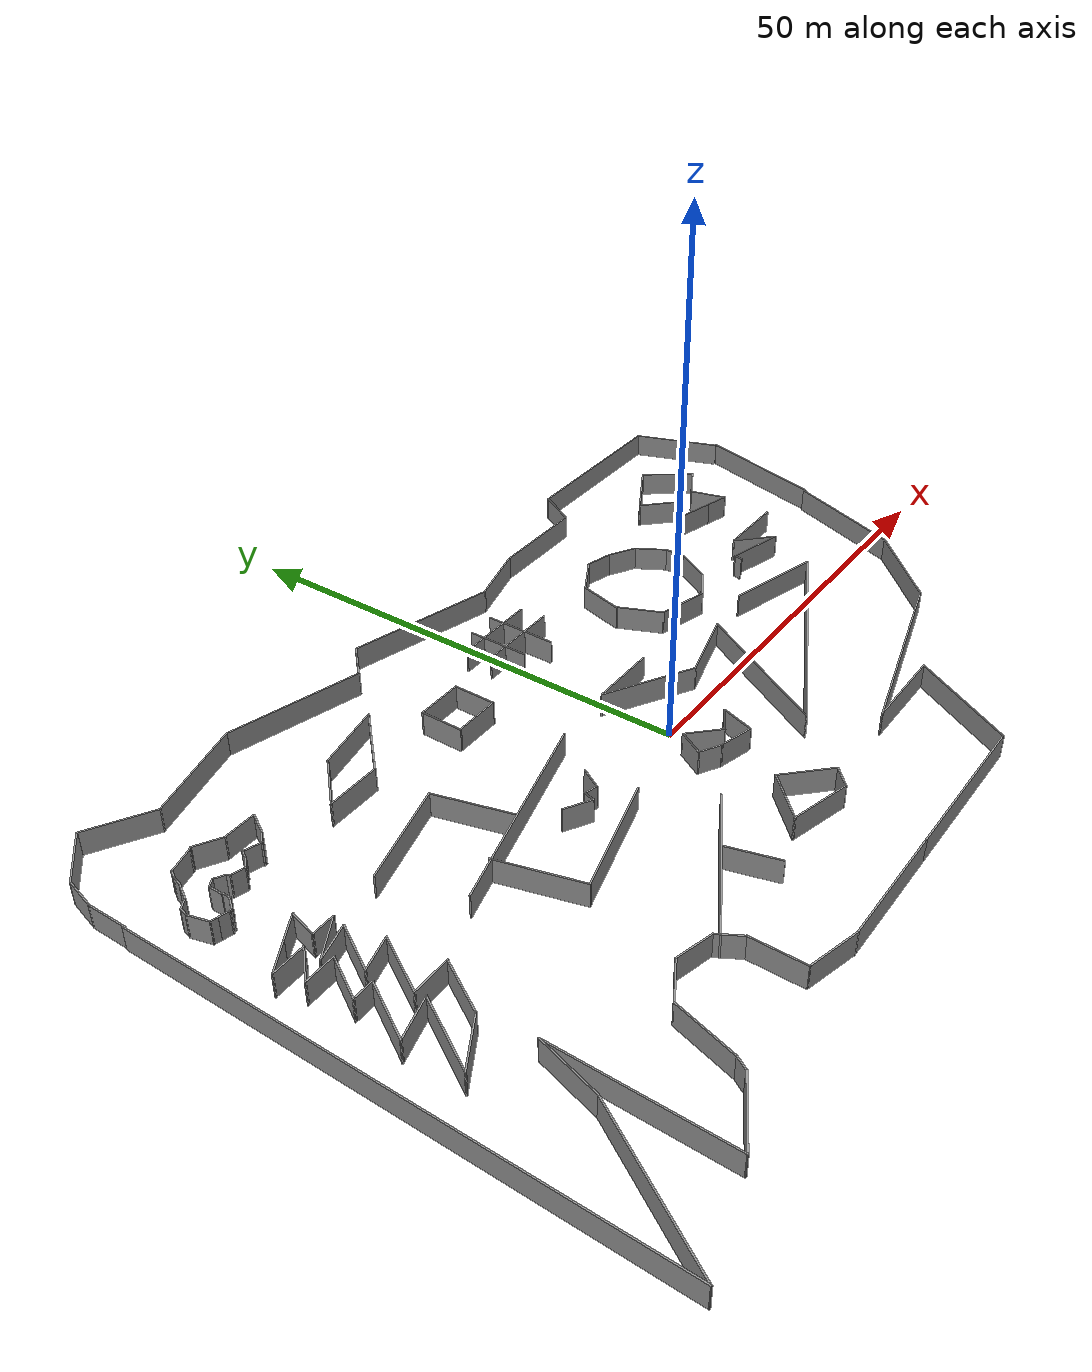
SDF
<?xml version='1.0'?>
<sdf version='1.7'>
  <model name='custommap5'>
    <pose>0.650434 0.198195 0 0 -0 0</pose>
    <link name='Wall_10'>
      <collision name='Wall_10_Collision'>
        <geometry>
          <box>
            <size>6.5 0.15 2.5</size>
          </box>
        </geometry>
        <pose>0 0 1.25 0 -0 0</pose>
      </collision>
      <visual name='Wall_10_Visual'>
        <pose>0 0 1.25 0 -0 0</pose>
        <geometry>
          <box>
            <size>6.5 0.15 2.5</size>
          </box>
        </geometry>
        <material>
          <script>
            <uri>file://media/materials/scripts/gazebo.material</uri>
            <name>Gazebo/Grey</name>
          </script>
          <ambient>1 1 1 1</ambient>
        </material>
        <meta>
          <layer>0</layer>
        </meta>
      </visual>
      <pose>-30.3175 -21.4493 0 0 -0 1.309</pose>
    </link>
    <link name='Wall_100'>
      <collision name='Wall_100_Collision'>
        <geometry>
          <box>
            <size>3.25 0.15 2.5</size>
          </box>
        </geometry>
        <pose>0 0 1.25 0 -0 0</pose>
      </collision>
      <visual name='Wall_100_Visual'>
        <pose>0 0 1.25 0 -0 0</pose>
        <geometry>
          <box>
            <size>3.25 0.15 2.5</size>
          </box>
        </geometry>
        <material>
          <script>
            <uri>file://media/materials/scripts/gazebo.material</uri>
            <name>Gazebo/Grey</name>
          </script>
          <ambient>1 1 1 1</ambient>
        </material>
        <meta>
          <layer>0</layer>
        </meta>
      </visual>
      <pose>-41.7743 4.90897 0 0 -0 0</pose>
    </link>
    <link name='Wall_101'>
      <collision name='Wall_101_Collision'>
        <geometry>
          <box>
            <size>4.75 0.15 2.5</size>
          </box>
        </geometry>
        <pose>0 0 1.25 0 -0 0</pose>
      </collision>
      <visual name='Wall_101_Visual'>
        <pose>0 0 1.25 0 -0 0</pose>
        <geometry>
          <box>
            <size>4.75 0.15 2.5</size>
          </box>
        </geometry>
        <material>
          <script>
            <uri>file://media/materials/scripts/gazebo.material</uri>
            <name>Gazebo/Grey</name>
          </script>
          <ambient>1 1 1 1</ambient>
        </material>
        <meta>
          <layer>0</layer>
        </meta>
      </visual>
      <pose>-41.3743 2.91711 0 0 -0 -2.0944</pose>
    </link>
    <link name='Wall_102'>
      <collision name='Wall_102_Collision'>
        <geometry>
          <box>
            <size>2.25 0.15 2.5</size>
          </box>
        </geometry>
        <pose>0 0 1.25 0 -0 0</pose>
      </collision>
      <visual name='Wall_102_Visual'>
        <pose>0 0 1.25 0 -0 0</pose>
        <geometry>
          <box>
            <size>2.25 0.15 2.5</size>
          </box>
        </geometry>
        <material>
          <script>
            <uri>file://media/materials/scripts/gazebo.material</uri>
            <name>Gazebo/Grey</name>
          </script>
          <ambient>1 1 1 1</ambient>
        </material>
        <meta>
          <layer>0</layer>
        </meta>
      </visual>
      <pose>-41.4743 0.925256 0 0 -0 0</pose>
    </link>
    <link name='Wall_103'>
      <collision name='Wall_103_Collision'>
        <geometry>
          <box>
            <size>6.25 0.15 2.5</size>
          </box>
        </geometry>
        <pose>0 0 1.25 0 -0 0</pose>
      </collision>
      <visual name='Wall_103_Visual'>
        <pose>0 0 1.25 0 -0 0</pose>
        <geometry>
          <box>
            <size>6.25 0.15 2.5</size>
          </box>
        </geometry>
        <material>
          <script>
            <uri>file://media/materials/scripts/gazebo.material</uri>
            <name>Gazebo/Grey</name>
          </script>
          <ambient>1 1 1 1</ambient>
        </material>
        <meta>
          <layer>0</layer>
        </meta>
      </visual>
      <pose>-41.9493 -1.71612 0 0 -0 -2.0944</pose>
    </link>
    <link name='Wall_104'>
      <collision name='Wall_104_Collision'>
        <geometry>
          <box>
            <size>4.5 0.15 2.5</size>
          </box>
        </geometry>
        <pose>0 0 1.25 0 -0 0</pose>
      </collision>
      <visual name='Wall_104_Visual'>
        <pose>0 0 1.25 0 -0 0</pose>
        <geometry>
          <box>
            <size>4.5 0.15 2.5</size>
          </box>
        </geometry>
        <material>
          <script>
            <uri>file://media/materials/scripts/gazebo.material</uri>
            <name>Gazebo/Grey</name>
          </script>
          <ambient>1 1 1 1</ambient>
        </material>
        <meta>
          <layer>0</layer>
        </meta>
      </visual>
      <pose>-41.3734 -3.79457 0 0 -0 0.261799</pose>
    </link>
    <link name='Wall_105'>
      <collision name='Wall_105_Collision'>
        <geometry>
          <box>
            <size>7.75 0.15 2.5</size>
          </box>
        </geometry>
        <pose>0 0 1.25 0 -0 0</pose>
      </collision>
      <visual name='Wall_105_Visual'>
        <pose>0 0 1.25 0 -0 0</pose>
        <geometry>
          <box>
            <size>7.75 0.15 2.5</size>
          </box>
        </geometry>
        <material>
          <script>
            <uri>file://media/materials/scripts/gazebo.material</uri>
            <name>Gazebo/Grey</name>
          </script>
          <ambient>1 1 1 1</ambient>
        </material>
        <meta>
          <layer>0</layer>
        </meta>
      </visual>
      <pose>-41.1725 -6.52253 0 0 -0 -2.0944</pose>
    </link>
    <link name='Wall_106'>
      <collision name='Wall_106_Collision'>
        <geometry>
          <box>
            <size>5.5 0.15 2.5</size>
          </box>
        </geometry>
        <pose>0 0 1.25 0 -0 0</pose>
      </collision>
      <visual name='Wall_106_Visual'>
        <pose>0 0 1.25 0 -0 0</pose>
        <geometry>
          <box>
            <size>5.5 0.15 2.5</size>
          </box>
        </geometry>
        <material>
          <script>
            <uri>file://media/materials/scripts/gazebo.material</uri>
            <name>Gazebo/Grey</name>
          </script>
          <ambient>1 1 1 1</ambient>
        </material>
        <meta>
          <layer>0</layer>
        </meta>
      </visual>
      <pose>-40.7559 -8.47593 0 0 -0 0.523599</pose>
    </link>
    <link name='Wall_107'>
      <collision name='Wall_107_Collision'>
        <geometry>
          <box>
            <size>5.75 0.15 2.5</size>
          </box>
        </geometry>
        <pose>0 0 1.25 0 -0 0</pose>
      </collision>
      <visual name='Wall_107_Visual'>
        <pose>0 0 1.25 0 -0 0</pose>
        <geometry>
          <box>
            <size>5.75 0.15 2.5</size>
          </box>
        </geometry>
        <material>
          <script>
            <uri>file://media/materials/scripts/gazebo.material</uri>
            <name>Gazebo/Grey</name>
          </script>
          <ambient>1 1 1 1</ambient>
        </material>
        <meta>
          <layer>0</layer>
        </meta>
      </visual>
      <pose>-37.0393 -4.71356 0 0 -0 1.0472</pose>
    </link>
    <link name='Wall_108'>
      <collision name='Wall_108_Collision'>
        <geometry>
          <box>
            <size>4 0.15 2.5</size>
          </box>
        </geometry>
        <pose>0 0 1.25 0 -0 0</pose>
      </collision>
      <visual name='Wall_108_Visual'>
        <pose>0 0 1.25 0 -0 0</pose>
        <geometry>
          <box>
            <size>4 0.15 2.5</size>
          </box>
        </geometry>
        <material>
          <script>
            <uri>file://media/materials/scripts/gazebo.material</uri>
            <name>Gazebo/Grey</name>
          </script>
          <ambient>1 1 1 1</ambient>
        </material>
        <meta>
          <layer>0</layer>
        </meta>
      </visual>
      <pose>-37.5643 -2.28869 0 0 -0 3.14159</pose>
    </link>
    <link name='Wall_109'>
      <collision name='Wall_109_Collision'>
        <geometry>
          <box>
            <size>6.25 0.15 2.5</size>
          </box>
        </geometry>
        <pose>0 0 1.25 0 -0 0</pose>
      </collision>
      <visual name='Wall_109_Visual'>
        <pose>0 0 1.25 0 -0 0</pose>
        <geometry>
          <box>
            <size>6.25 0.15 2.5</size>
          </box>
        </geometry>
        <material>
          <script>
            <uri>file://media/materials/scripts/gazebo.material</uri>
            <name>Gazebo/Grey</name>
          </script>
          <ambient>1 1 1 1</ambient>
        </material>
        <meta>
          <layer>0</layer>
        </meta>
      </visual>
      <pose>-37.9643 0.352691 0 0 -0 1.0472</pose>
    </link>
    <link name='Wall_11'>
      <collision name='Wall_11_Collision'>
        <geometry>
          <box>
            <size>4.5 0.15 2.5</size>
          </box>
        </geometry>
        <pose>0 0 1.25 0 -0 0</pose>
      </collision>
      <visual name='Wall_11_Visual'>
        <pose>0 0 1.25 0 -0 0</pose>
        <geometry>
          <box>
            <size>4.5 0.15 2.5</size>
          </box>
        </geometry>
        <material>
          <script>
            <uri>file://media/materials/scripts/gazebo.material</uri>
            <name>Gazebo/Grey</name>
          </script>
          <ambient>1 1 1 1</ambient>
        </material>
        <meta>
          <layer>0</layer>
        </meta>
      </visual>
      <pose>-27.6121 -17.295 0 0 -0 0.523599</pose>
    </link>
    <link name='Wall_110'>
      <collision name='Wall_110_Collision'>
        <geometry>
          <box>
            <size>3.75 0.15 2.5</size>
          </box>
        </geometry>
        <pose>0 0 1.25 0 -0 0</pose>
      </collision>
      <visual name='Wall_110_Visual'>
        <pose>0 0 1.25 0 -0 0</pose>
        <geometry>
          <box>
            <size>3.75 0.15 2.5</size>
          </box>
        </geometry>
        <material>
          <script>
            <uri>file://media/materials/scripts/gazebo.material</uri>
            <name>Gazebo/Grey</name>
          </script>
          <ambient>1 1 1 1</ambient>
        </material>
        <meta>
          <layer>0</layer>
        </meta>
      </visual>
      <pose>-38.1779 2.52819 0 0 -0 -2.87979</pose>
    </link>
    <link name='Wall_111'>
      <collision name='Wall_111_Collision'>
        <geometry>
          <box>
            <size>5.25 0.15 2.5</size>
          </box>
        </geometry>
        <pose>0 0 1.25 0 -0 0</pose>
      </collision>
      <visual name='Wall_111_Visual'>
        <pose>0 0 1.25 0 -0 0</pose>
        <geometry>
          <box>
            <size>5.25 0.15 2.5</size>
          </box>
        </geometry>
        <material>
          <script>
            <uri>file://media/materials/scripts/gazebo.material</uri>
            <name>Gazebo/Grey</name>
          </script>
          <ambient>1 1 1 1</ambient>
        </material>
        <meta>
          <layer>0</layer>
        </meta>
      </visual>
      <pose>-38.6416 4.27068 0 0 -0 1.0472</pose>
    </link>
    <link name='Wall_112'>
      <collision name='Wall_112_Collision'>
        <geometry>
          <box>
            <size>4 0.15 2.5</size>
          </box>
        </geometry>
        <pose>0 0 1.25 0 -0 0</pose>
      </collision>
      <visual name='Wall_112_Visual'>
        <pose>0 0 1.25 0 -0 0</pose>
        <geometry>
          <box>
            <size>4 0.15 2.5</size>
          </box>
        </geometry>
        <material>
          <script>
            <uri>file://media/materials/scripts/gazebo.material</uri>
            <name>Gazebo/Grey</name>
          </script>
          <ambient>1 1 1 1</ambient>
        </material>
        <meta>
          <layer>0</layer>
        </meta>
      </visual>
      <pose>-39.226 5.98082 0 0 -0 -2.87979</pose>
    </link>
    <link name='Wall_113'>
      <collision name='Wall_113_Collision'>
        <geometry>
          <box>
            <size>4.75 0.15 2.5</size>
          </box>
        </geometry>
        <pose>0 0 1.25 0 -0 0</pose>
      </collision>
      <visual name='Wall_113_Visual'>
        <pose>0 0 1.25 0 -0 0</pose>
        <geometry>
          <box>
            <size>4.75 0.15 2.5</size>
          </box>
        </geometry>
        <material>
          <script>
            <uri>file://media/materials/scripts/gazebo.material</uri>
            <name>Gazebo/Grey</name>
          </script>
          <ambient>1 1 1 1</ambient>
        </material>
        <meta>
          <layer>0</layer>
        </meta>
      </visual>
      <pose>-39.0936 6.6326 0 0 -0 0.523599</pose>
    </link>
    <link name='Wall_114'>
      <collision name='Wall_114_Collision'>
        <geometry>
          <box>
            <size>2.5 0.15 2.5</size>
          </box>
        </geometry>
        <pose>0 0 1.25 0 -0 0</pose>
      </collision>
      <visual name='Wall_114_Visual'>
        <pose>0 0 1.25 0 -0 0</pose>
        <geometry>
          <box>
            <size>2.5 0.15 2.5</size>
          </box>
        </geometry>
        <material>
          <script>
            <uri>file://media/materials/scripts/gazebo.material</uri>
            <name>Gazebo/Grey</name>
          </script>
          <ambient>1 1 1 1</ambient>
        </material>
        <meta>
          <layer>0</layer>
        </meta>
      </visual>
      <pose>-38.2767 7.7826 0 0 -0 3.14159</pose>
    </link>
    <link name='Wall_115'>
      <collision name='Wall_115_Collision'>
        <geometry>
          <box>
            <size>3 0.15 2.5</size>
          </box>
        </geometry>
        <pose>0 0 1.25 0 -0 0</pose>
      </collision>
      <visual name='Wall_115_Visual'>
        <pose>0 0 1.25 0 -0 0</pose>
        <geometry>
          <box>
            <size>3 0.15 2.5</size>
          </box>
        </geometry>
        <material>
          <script>
            <uri>file://media/materials/scripts/gazebo.material</uri>
            <name>Gazebo/Grey</name>
          </script>
          <ambient>1 1 1 1</ambient>
        </material>
        <meta>
          <layer>0</layer>
        </meta>
      </visual>
      <pose>-39.0829 9.15904 0 0 -0 1.309</pose>
    </link>
    <link name='Wall_116'>
      <collision name='Wall_116_Collision'>
        <geometry>
          <box>
            <size>3.02994 0.15 2.5</size>
          </box>
        </geometry>
        <pose>0 0 1.25 0 -0 0</pose>
      </collision>
      <visual name='Wall_116_Visual'>
        <pose>0 0 1.25 0 -0 0</pose>
        <geometry>
          <box>
            <size>3.02994 0.15 2.5</size>
          </box>
        </geometry>
        <material>
          <script>
            <uri>file://media/materials/scripts/gazebo.material</uri>
            <name>Gazebo/Grey</name>
          </script>
          <ambient>1 1 1 1</ambient>
        </material>
        <meta>
          <layer>0</layer>
        </meta>
      </visual>
      <pose>-39.9708 9.83252 0 0 -0 -2.63159</pose>
    </link>
    <link name='Wall_118'>
      <collision name='Wall_118_Collision'>
        <geometry>
          <box>
            <size>3 0.15 2.5</size>
          </box>
        </geometry>
        <pose>0 0 1.25 0 -0 0</pose>
      </collision>
      <visual name='Wall_118_Visual'>
        <pose>0 0 1.25 0 -0 0</pose>
        <geometry>
          <box>
            <size>3 0.15 2.5</size>
          </box>
        </geometry>
        <material>
          <script>
            <uri>file://media/materials/scripts/gazebo.material</uri>
            <name>Gazebo/Grey</name>
          </script>
          <ambient>1 1 1 1</ambient>
        </material>
        <meta>
          <layer>0</layer>
        </meta>
      </visual>
      <pose>1.5599 -4.60224 0 0 -0 -2.61799</pose>
    </link>
    <link name='Wall_119'>
      <collision name='Wall_119_Collision'>
        <geometry>
          <box>
            <size>4 0.15 2.5</size>
          </box>
        </geometry>
        <pose>0 0 1.25 0 -0 0</pose>
      </collision>
      <visual name='Wall_119_Visual'>
        <pose>0 0 1.25 0 -0 0</pose>
        <geometry>
          <box>
            <size>4 0.15 2.5</size>
          </box>
        </geometry>
        <material>
          <script>
            <uri>file://media/materials/scripts/gazebo.material</uri>
            <name>Gazebo/Grey</name>
          </script>
          <ambient>1 1 1 1</ambient>
        </material>
        <meta>
          <layer>0</layer>
        </meta>
      </visual>
      <pose>-1.03537 -3.95356 0 0 -0 2.35619</pose>
    </link>
    <link name='Wall_12'>
      <collision name='Wall_12_Collision'>
        <geometry>
          <box>
            <size>4 0.15 2.5</size>
          </box>
        </geometry>
        <pose>0 0 1.25 0 -0 0</pose>
      </collision>
      <visual name='Wall_12_Visual'>
        <pose>0 0 1.25 0 -0 0</pose>
        <geometry>
          <box>
            <size>4 0.15 2.5</size>
          </box>
        </geometry>
        <material>
          <script>
            <uri>file://media/materials/scripts/gazebo.material</uri>
            <name>Gazebo/Grey</name>
          </script>
          <ambient>1 1 1 1</ambient>
        </material>
        <meta>
          <layer>0</layer>
        </meta>
      </visual>
      <pose>-23.8691 -16.7057 0 0 -0 -0.261799</pose>
    </link>
    <link name='Wall_120'>
      <collision name='Wall_120_Collision'>
        <geometry>
          <box>
            <size>3 0.15 2.5</size>
          </box>
        </geometry>
        <pose>0 0 1.25 0 -0 0</pose>
      </collision>
      <visual name='Wall_120_Visual'>
        <pose>0 0 1.25 0 -0 0</pose>
        <geometry>
          <box>
            <size>3 0.15 2.5</size>
          </box>
        </geometry>
        <material>
          <script>
            <uri>file://media/materials/scripts/gazebo.material</uri>
            <name>Gazebo/Grey</name>
          </script>
          <ambient>1 1 1 1</ambient>
        </material>
        <meta>
          <layer>0</layer>
        </meta>
      </visual>
      <pose>-3.10905 -3.82647 0 0 -0 -2.0944</pose>
    </link>
    <link name='Wall_121'>
      <collision name='Wall_121_Collision'>
        <geometry>
          <box>
            <size>2.5 0.15 2.5</size>
          </box>
        </geometry>
        <pose>0 0 1.25 0 -0 0</pose>
      </collision>
      <visual name='Wall_121_Visual'>
        <pose>0 0 1.25 0 -0 0</pose>
        <geometry>
          <box>
            <size>2.5 0.15 2.5</size>
          </box>
        </geometry>
        <material>
          <script>
            <uri>file://media/materials/scripts/gazebo.material</uri>
            <name>Gazebo/Grey</name>
          </script>
          <ambient>1 1 1 1</ambient>
        </material>
        <meta>
          <layer>0</layer>
        </meta>
      </visual>
      <pose>-2.80397 -5.64805 0 0 -0 -0.523599</pose>
    </link>
    <link name='Wall_122'>
      <collision name='Wall_122_Collision'>
        <geometry>
          <box>
            <size>3.75 0.15 2.5</size>
          </box>
        </geometry>
        <pose>0 0 1.25 0 -0 0</pose>
      </collision>
      <visual name='Wall_122_Visual'>
        <pose>0 0 1.25 0 -0 0</pose>
        <geometry>
          <box>
            <size>3.75 0.15 2.5</size>
          </box>
        </geometry>
        <material>
          <script>
            <uri>file://media/materials/scripts/gazebo.material</uri>
            <name>Gazebo/Grey</name>
          </script>
          <ambient>1 1 1 1</ambient>
        </material>
        <meta>
          <layer>0</layer>
        </meta>
      </visual>
      <pose>-0.047719 -6.70143 0 0 -0 -0.261799</pose>
    </link>
    <link name='Wall_123'>
      <collision name='Wall_123_Collision'>
        <geometry>
          <box>
            <size>3.60819 0.15 2.5</size>
          </box>
        </geometry>
        <pose>0 0 1.25 0 -0 0</pose>
      </collision>
      <visual name='Wall_123_Visual'>
        <pose>0 0 1.25 0 -0 0</pose>
        <geometry>
          <box>
            <size>3.60819 0.15 2.5</size>
          </box>
        </geometry>
        <material>
          <script>
            <uri>file://media/materials/scripts/gazebo.material</uri>
            <name>Gazebo/Grey</name>
          </script>
          <ambient>1 1 1 1</ambient>
        </material>
        <meta>
          <layer>0</layer>
        </meta>
      </visual>
      <pose>2.24247 -5.52852 0 0 -0 1.24616</pose>
    </link>
    <link name='Wall_125'>
      <collision name='Wall_125_Collision'>
        <geometry>
          <box>
            <size>7.25 0.15 2.5</size>
          </box>
        </geometry>
        <pose>0 0 1.25 0 -0 0</pose>
      </collision>
      <visual name='Wall_125_Visual'>
        <pose>0 0 1.25 0 -0 0</pose>
        <geometry>
          <box>
            <size>7.25 0.15 2.5</size>
          </box>
        </geometry>
        <material>
          <script>
            <uri>file://media/materials/scripts/gazebo.material</uri>
            <name>Gazebo/Grey</name>
          </script>
          <ambient>1 1 1 1</ambient>
        </material>
        <meta>
          <layer>0</layer>
        </meta>
      </visual>
      <pose>1.84785 6.60707 0 0 -0 3.14159</pose>
    </link>
    <link name='Wall_126'>
      <collision name='Wall_126_Collision'>
        <geometry>
          <box>
            <size>10 0.15 2.5</size>
          </box>
        </geometry>
        <pose>0 0 1.25 0 -0 0</pose>
      </collision>
      <visual name='Wall_126_Visual'>
        <pose>0 0 1.25 0 -0 0</pose>
        <geometry>
          <box>
            <size>10 0.15 2.5</size>
          </box>
        </geometry>
        <material>
          <script>
            <uri>file://media/materials/scripts/gazebo.material</uri>
            <name>Gazebo/Grey</name>
          </script>
          <ambient>1 1 1 1</ambient>
        </material>
        <meta>
          <layer>0</layer>
        </meta>
      </visual>
      <pose>2.56302 4.14457 0 0 -0 -0.523599</pose>
    </link>
    <link name='Wall_127'>
      <collision name='Wall_127_Collision'>
        <geometry>
          <box>
            <size>8 0.15 2.5</size>
          </box>
        </geometry>
        <pose>0 0 1.25 0 -0 0</pose>
      </collision>
      <visual name='Wall_127_Visual'>
        <pose>0 0 1.25 0 -0 0</pose>
        <geometry>
          <box>
            <size>8 0.15 2.5</size>
          </box>
        </geometry>
        <material>
          <script>
            <uri>file://media/materials/scripts/gazebo.material</uri>
            <name>Gazebo/Grey</name>
          </script>
          <ambient>1 1 1 1</ambient>
        </material>
        <meta>
          <layer>0</layer>
        </meta>
      </visual>
      <pose>10.6195 2.69793 0 0 -0 0.261799</pose>
    </link>
    <link name='Wall_128'>
      <collision name='Wall_128_Collision'>
        <geometry>
          <box>
            <size>16.5 0.15 2.5</size>
          </box>
        </geometry>
        <pose>0 0 1.25 0 -0 0</pose>
      </collision>
      <visual name='Wall_128_Visual'>
        <pose>0 0 1.25 0 -0 0</pose>
        <geometry>
          <box>
            <size>16.5 0.15 2.5</size>
          </box>
        </geometry>
        <material>
          <script>
            <uri>file://media/materials/scripts/gazebo.material</uri>
            <name>Gazebo/Grey</name>
          </script>
          <ambient>1 1 1 1</ambient>
        </material>
        <meta>
          <layer>0</layer>
        </meta>
      </visual>
      <pose>10.3232 -3.36596 0 0 -0 -2.0944</pose>
    </link>
    <link name='Wall_129'>
      <collision name='Wall_129_Collision'>
        <geometry>
          <box>
            <size>26.8353 0.15 2.5</size>
          </box>
        </geometry>
        <pose>0 0 1.25 0 -0 0</pose>
      </collision>
      <visual name='Wall_129_Visual'>
        <pose>0 0 1.25 0 -0 0</pose>
        <geometry>
          <box>
            <size>26.8353 0.15 2.5</size>
          </box>
        </geometry>
        <material>
          <script>
            <uri>file://media/materials/scripts/gazebo.material</uri>
            <name>Gazebo/Grey</name>
          </script>
          <ambient>1 1 1 1</ambient>
        </material>
        <meta>
          <layer>0</layer>
        </meta>
      </visual>
      <pose>18.0786 -4.29987 0 0 -0 0.478691</pose>
    </link>
    <link name='Wall_13'>
      <collision name='Wall_13_Collision'>
        <geometry>
          <box>
            <size>2.75 0.15 2.5</size>
          </box>
        </geometry>
        <pose>0 0 1.25 0 -0 0</pose>
      </collision>
      <visual name='Wall_13_Visual'>
        <pose>0 0 1.25 0 -0 0</pose>
        <geometry>
          <box>
            <size>2.75 0.15 2.5</size>
          </box>
        </geometry>
        <material>
          <script>
            <uri>file://media/materials/scripts/gazebo.material</uri>
            <name>Gazebo/Grey</name>
          </script>
          <ambient>1 1 1 1</ambient>
        </material>
        <meta>
          <layer>0</layer>
        </meta>
      </visual>
      <pose>-21.3597 -18.3297 0 0 -0 -1.0472</pose>
    </link>
    <link name='Wall_130'>
      <collision name='Wall_130_Collision'>
        <geometry>
          <box>
            <size>10.25 0.15 2.5</size>
          </box>
        </geometry>
        <pose>0 0 1.25 0 -0 0</pose>
      </collision>
      <visual name='Wall_130_Visual'>
        <pose>0 0 1.25 0 -0 0</pose>
        <geometry>
          <box>
            <size>10.25 0.15 2.5</size>
          </box>
        </geometry>
        <material>
          <script>
            <uri>file://media/materials/scripts/gazebo.material</uri>
            <name>Gazebo/Grey</name>
          </script>
          <ambient>1 1 1 1</ambient>
        </material>
        <meta>
          <layer>0</layer>
        </meta>
      </visual>
      <pose>24.9622 3.15302 0 0 -0 2.87979</pose>
    </link>
    <link name='Wall_132'>
      <collision name='Wall_132_Collision'>
        <geometry>
          <box>
            <size>16.5 0.15 2.5</size>
          </box>
        </geometry>
        <pose>0 0 1.25 0 -0 0</pose>
      </collision>
      <visual name='Wall_132_Visual'>
        <pose>0 0 1.25 0 -0 0</pose>
        <geometry>
          <box>
            <size>16.5 0.15 2.5</size>
          </box>
        </geometry>
        <material>
          <script>
            <uri>file://media/materials/scripts/gazebo.material</uri>
            <name>Gazebo/Grey</name>
          </script>
          <ambient>1 1 1 1</ambient>
        </material>
        <meta>
          <layer>0</layer>
        </meta>
      </visual>
      <pose>-14.7012 -13.6732 0 0 -0 -2.61799</pose>
    </link>
    <link name='Wall_134'>
      <collision name='Wall_134_Collision'>
        <geometry>
          <box>
            <size>5.25 0.15 2.5</size>
          </box>
        </geometry>
        <pose>0 0 1.25 0 -0 0</pose>
      </collision>
      <visual name='Wall_134_Visual'>
        <pose>0 0 1.25 0 -0 0</pose>
        <geometry>
          <box>
            <size>5.25 0.15 2.5</size>
          </box>
        </geometry>
        <material>
          <script>
            <uri>file://media/materials/scripts/gazebo.material</uri>
            <name>Gazebo/Grey</name>
          </script>
          <ambient>1 1 1 1</ambient>
        </material>
        <meta>
          <layer>0</layer>
        </meta>
      </visual>
      <pose>-12.4133 -15.385 0 0 -0 -1.309</pose>
    </link>
    <link name='Wall_136'>
      <collision name='Wall_136_Collision'>
        <geometry>
          <box>
            <size>5.75 0.15 2.5</size>
          </box>
        </geometry>
        <pose>0 0 1.25 0 -0 0</pose>
      </collision>
      <visual name='Wall_136_Visual'>
        <pose>0 0 1.25 0 -0 0</pose>
        <geometry>
          <box>
            <size>5.75 0.15 2.5</size>
          </box>
        </geometry>
        <material>
          <script>
            <uri>file://media/materials/scripts/gazebo.material</uri>
            <name>Gazebo/Grey</name>
          </script>
          <ambient>1 1 1 1</ambient>
        </material>
        <meta>
          <layer>0</layer>
        </meta>
      </visual>
      <pose>-0.731953 -14.1154 0 0 -0 2.35619</pose>
    </link>
    <link name='Wall_137'>
      <collision name='Wall_137_Collision'>
        <geometry>
          <box>
            <size>5.75 0.15 2.5</size>
          </box>
        </geometry>
        <pose>0 0 1.25 0 -0 0</pose>
      </collision>
      <visual name='Wall_137_Visual'>
        <pose>0 0 1.25 0 -0 0</pose>
        <geometry>
          <box>
            <size>5.75 0.15 2.5</size>
          </box>
        </geometry>
        <material>
          <script>
            <uri>file://media/materials/scripts/gazebo.material</uri>
            <name>Gazebo/Grey</name>
          </script>
          <ambient>1 1 1 1</ambient>
        </material>
        <meta>
          <layer>0</layer>
        </meta>
      </visual>
      <pose>-4.69175 -14.1154 0 0 -0 -2.35619</pose>
    </link>
    <link name='Wall_138'>
      <collision name='Wall_138_Collision'>
        <geometry>
          <box>
            <size>6.5 0.15 2.5</size>
          </box>
        </geometry>
        <pose>0 0 1.25 0 -0 0</pose>
      </collision>
      <visual name='Wall_138_Visual'>
        <pose>0 0 1.25 0 -0 0</pose>
        <geometry>
          <box>
            <size>6.5 0.15 2.5</size>
          </box>
        </geometry>
        <material>
          <script>
            <uri>file://media/materials/scripts/gazebo.material</uri>
            <name>Gazebo/Grey</name>
          </script>
          <ambient>1 1 1 1</ambient>
        </material>
        <meta>
          <layer>0</layer>
        </meta>
      </visual>
      <pose>-3.60484 -16.9171 0 0 -0 -0.261799</pose>
    </link>
    <link name='Wall_139'>
      <collision name='Wall_139_Collision'>
        <geometry>
          <box>
            <size>2.57709 0.15 2.5</size>
          </box>
        </geometry>
        <pose>0 0 1.25 0 -0 0</pose>
      </collision>
      <visual name='Wall_139_Visual'>
        <pose>0 0 1.25 0 -0 0</pose>
        <geometry>
          <box>
            <size>2.57709 0.15 2.5</size>
          </box>
        </geometry>
        <material>
          <script>
            <uri>file://media/materials/scripts/gazebo.material</uri>
            <name>Gazebo/Grey</name>
          </script>
          <ambient>1 1 1 1</ambient>
        </material>
        <meta>
          <layer>0</layer>
        </meta>
      </visual>
      <pose>0.354963 -16.9171 0 0 -0 0.74388</pose>
    </link>
    <link name='Wall_14'>
      <collision name='Wall_14_Collision'>
        <geometry>
          <box>
            <size>5.5 0.15 2.5</size>
          </box>
        </geometry>
        <pose>0 0 1.25 0 -0 0</pose>
      </collision>
      <visual name='Wall_14_Visual'>
        <pose>0 0 1.25 0 -0 0</pose>
        <geometry>
          <box>
            <size>5.5 0.15 2.5</size>
          </box>
        </geometry>
        <material>
          <script>
            <uri>file://media/materials/scripts/gazebo.material</uri>
            <name>Gazebo/Grey</name>
          </script>
          <ambient>1 1 1 1</ambient>
        </material>
        <meta>
          <layer>0</layer>
        </meta>
      </visual>
      <pose>-20.7097 -22.1306 0 0 -0 -1.5708</pose>
    </link>
    <link name='Wall_141'>
      <collision name='Wall_141_Collision'>
        <geometry>
          <box>
            <size>6 0.15 2.5</size>
          </box>
        </geometry>
        <pose>0 0 1.25 0 -0 0</pose>
      </collision>
      <visual name='Wall_141_Visual'>
        <pose>0 0 1.25 0 -0 0</pose>
        <geometry>
          <box>
            <size>6 0.15 2.5</size>
          </box>
        </geometry>
        <material>
          <script>
            <uri>file://media/materials/scripts/gazebo.material</uri>
            <name>Gazebo/Grey</name>
          </script>
          <ambient>1 1 1 1</ambient>
        </material>
        <meta>
          <layer>0</layer>
        </meta>
      </visual>
      <pose>-25.3943 18.86 0 0 -0 -2.35619</pose>
    </link>
    <link name='Wall_142'>
      <collision name='Wall_142_Collision'>
        <geometry>
          <box>
            <size>5.75 0.15 2.5</size>
          </box>
        </geometry>
        <pose>0 0 1.25 0 -0 0</pose>
      </collision>
      <visual name='Wall_142_Visual'>
        <pose>0 0 1.25 0 -0 0</pose>
        <geometry>
          <box>
            <size>5.75 0.15 2.5</size>
          </box>
        </geometry>
        <material>
          <script>
            <uri>file://media/materials/scripts/gazebo.material</uri>
            <name>Gazebo/Grey</name>
          </script>
          <ambient>1 1 1 1</ambient>
        </material>
        <meta>
          <layer>0</layer>
        </meta>
      </visual>
      <pose>-24.6626 16.7917 0 0 -0 0</pose>
    </link>
    <link name='Wall_143'>
      <collision name='Wall_143_Collision'>
        <geometry>
          <box>
            <size>8 0.15 2.5</size>
          </box>
        </geometry>
        <pose>0 0 1.25 0 -0 0</pose>
      </collision>
      <visual name='Wall_143_Visual'>
        <pose>0 0 1.25 0 -0 0</pose>
        <geometry>
          <box>
            <size>8 0.15 2.5</size>
          </box>
        </geometry>
        <material>
          <script>
            <uri>file://media/materials/scripts/gazebo.material</uri>
            <name>Gazebo/Grey</name>
          </script>
          <ambient>1 1 1 1</ambient>
        </material>
        <meta>
          <layer>0</layer>
        </meta>
      </visual>
      <pose>-19.0872 19.5671 0 0 -0 0.785398</pose>
    </link>
    <link name='Wall_144'>
      <collision name='Wall_144_Collision'>
        <geometry>
          <box>
            <size>7.30536 0.15 2.5</size>
          </box>
        </geometry>
        <pose>0 0 1.25 0 -0 0</pose>
      </collision>
      <visual name='Wall_144_Visual'>
        <pose>0 0 1.25 0 -0 0</pose>
        <geometry>
          <box>
            <size>7.30536 0.15 2.5</size>
          </box>
        </geometry>
        <material>
          <script>
            <uri>file://media/materials/scripts/gazebo.material</uri>
            <name>Gazebo/Grey</name>
          </script>
          <ambient>1 1 1 1</ambient>
        </material>
        <meta>
          <layer>0</layer>
        </meta>
      </visual>
      <pose>-19.8189 21.6354 0 0 -0 -2.94264</pose>
    </link>
    <link name='Wall_146'>
      <collision name='Wall_146_Collision'>
        <geometry>
          <box>
            <size>6.5 0.15 2.5</size>
          </box>
        </geometry>
        <pose>0 0 1.25 0 -0 0</pose>
      </collision>
      <visual name='Wall_146_Visual'>
        <pose>0 0 1.25 0 -0 0</pose>
        <geometry>
          <box>
            <size>6.5 0.15 2.5</size>
          </box>
        </geometry>
        <material>
          <script>
            <uri>file://media/materials/scripts/gazebo.material</uri>
            <name>Gazebo/Grey</name>
          </script>
          <ambient>1 1 1 1</ambient>
        </material>
        <meta>
          <layer>0</layer>
        </meta>
      </visual>
      <pose>-0.631779 19.4863 0 0 -0 -1.5708</pose>
    </link>
    <link name='Wall_148'>
      <collision name='Wall_148_Collision'>
        <geometry>
          <box>
            <size>7.5 0.15 2.5</size>
          </box>
        </geometry>
        <pose>0 0 1.25 0 -0 0</pose>
      </collision>
      <visual name='Wall_148_Visual'>
        <pose>0 0 1.25 0 -0 0</pose>
        <geometry>
          <box>
            <size>7.5 0.15 2.5</size>
          </box>
        </geometry>
        <material>
          <script>
            <uri>file://media/materials/scripts/gazebo.material</uri>
            <name>Gazebo/Grey</name>
          </script>
          <ambient>1 1 1 1</ambient>
        </material>
        <meta>
          <layer>0</layer>
        </meta>
      </visual>
      <pose>2.48899 19.0939 0 0 -0 -1.5708</pose>
    </link>
    <link name='Wall_15'>
      <collision name='Wall_15_Collision'>
        <geometry>
          <box>
            <size>5.5 0.15 2.5</size>
          </box>
        </geometry>
        <pose>0 0 1.25 0 -0 0</pose>
      </collision>
      <visual name='Wall_15_Visual'>
        <pose>0 0 1.25 0 -0 0</pose>
        <geometry>
          <box>
            <size>5.5 0.15 2.5</size>
          </box>
        </geometry>
        <material>
          <script>
            <uri>file://media/materials/scripts/gazebo.material</uri>
            <name>Gazebo/Grey</name>
          </script>
          <ambient>1 1 1 1</ambient>
        </material>
        <meta>
          <layer>0</layer>
        </meta>
      </visual>
      <pose>-18.1258 -25.4979 0 0 -0 -0.261799</pose>
    </link>
    <link name='Wall_150'>
      <collision name='Wall_150_Collision'>
        <geometry>
          <box>
            <size>8.75 0.15 2.5</size>
          </box>
        </geometry>
        <pose>0 0 1.25 0 -0 0</pose>
      </collision>
      <visual name='Wall_150_Visual'>
        <pose>0 0 1.25 0 -0 0</pose>
        <geometry>
          <box>
            <size>8.75 0.15 2.5</size>
          </box>
        </geometry>
        <material>
          <script>
            <uri>file://media/materials/scripts/gazebo.material</uri>
            <name>Gazebo/Grey</name>
          </script>
          <ambient>1 1 1 1</ambient>
        </material>
        <meta>
          <layer>0</layer>
        </meta>
      </visual>
      <pose>1.08552 21.1547 0 0 -0 0</pose>
    </link>
    <link name='Wall_152'>
      <collision name='Wall_152_Collision'>
        <geometry>
          <box>
            <size>8.75 0.15 2.5</size>
          </box>
        </geometry>
        <pose>0 0 1.25 0 -0 0</pose>
      </collision>
      <visual name='Wall_152_Visual'>
        <pose>0 0 1.25 0 -0 0</pose>
        <geometry>
          <box>
            <size>8.75 0.15 2.5</size>
          </box>
        </geometry>
        <material>
          <script>
            <uri>file://media/materials/scripts/gazebo.material</uri>
            <name>Gazebo/Grey</name>
          </script>
          <ambient>1 1 1 1</ambient>
        </material>
        <meta>
          <layer>0</layer>
        </meta>
      </visual>
      <pose>1.40836 18.572 0 0 -0 0</pose>
    </link>
    <link name='Wall_154'>
      <collision name='Wall_154_Collision'>
        <geometry>
          <box>
            <size>7.25 0.15 2.5</size>
          </box>
        </geometry>
        <pose>0 0 1.25 0 -0 0</pose>
      </collision>
      <visual name='Wall_154_Visual'>
        <pose>0 0 1.25 0 -0 0</pose>
        <geometry>
          <box>
            <size>7.25 0.15 2.5</size>
          </box>
        </geometry>
        <material>
          <script>
            <uri>file://media/materials/scripts/gazebo.material</uri>
            <name>Gazebo/Grey</name>
          </script>
          <ambient>1 1 1 1</ambient>
        </material>
        <meta>
          <layer>0</layer>
        </meta>
      </visual>
      <pose>32.8624 24.4607 0 0 -0 -2.61799</pose>
    </link>
    <link name='Wall_155'>
      <collision name='Wall_155_Collision'>
        <geometry>
          <box>
            <size>4.25 0.15 2.5</size>
          </box>
        </geometry>
        <pose>0 0 1.25 0 -0 0</pose>
      </collision>
      <visual name='Wall_155_Visual'>
        <pose>0 0 1.25 0 -0 0</pose>
        <geometry>
          <box>
            <size>4.25 0.15 2.5</size>
          </box>
        </geometry>
        <material>
          <script>
            <uri>file://media/materials/scripts/gazebo.material</uri>
            <name>Gazebo/Grey</name>
          </script>
          <ambient>1 1 1 1</ambient>
        </material>
        <meta>
          <layer>0</layer>
        </meta>
      </visual>
      <pose>31.2375 21.2362 0 0 -0 -0.785398</pose>
    </link>
    <link name='Wall_156'>
      <collision name='Wall_156_Collision'>
        <geometry>
          <box>
            <size>4 0.15 2.5</size>
          </box>
        </geometry>
        <pose>0 0 1.25 0 -0 0</pose>
      </collision>
      <visual name='Wall_156_Visual'>
        <pose>0 0 1.25 0 -0 0</pose>
        <geometry>
          <box>
            <size>4 0.15 2.5</size>
          </box>
        </geometry>
        <material>
          <script>
            <uri>file://media/materials/scripts/gazebo.material</uri>
            <name>Gazebo/Grey</name>
          </script>
          <ambient>1 1 1 1</ambient>
        </material>
        <meta>
          <layer>0</layer>
        </meta>
      </visual>
      <pose>31.02 18.8241 0 0 -0 -2.61799</pose>
    </link>
    <link name='Wall_157'>
      <collision name='Wall_157_Collision'>
        <geometry>
          <box>
            <size>5.25 0.15 2.5</size>
          </box>
        </geometry>
        <pose>0 0 1.25 0 -0 0</pose>
      </collision>
      <visual name='Wall_157_Visual'>
        <pose>0 0 1.25 0 -0 0</pose>
        <geometry>
          <box>
            <size>5.25 0.15 2.5</size>
          </box>
        </geometry>
        <material>
          <script>
            <uri>file://media/materials/scripts/gazebo.material</uri>
            <name>Gazebo/Grey</name>
          </script>
          <ambient>1 1 1 1</ambient>
        </material>
        <meta>
          <layer>0</layer>
        </meta>
      </visual>
      <pose>31.816 17.2016 0 0 -0 -0.261799</pose>
    </link>
    <link name='Wall_158'>
      <collision name='Wall_158_Collision'>
        <geometry>
          <box>
            <size>2.75 0.15 2.5</size>
          </box>
        </geometry>
        <pose>0 0 1.25 0 -0 0</pose>
      </collision>
      <visual name='Wall_158_Visual'>
        <pose>0 0 1.25 0 -0 0</pose>
        <geometry>
          <box>
            <size>2.75 0.15 2.5</size>
          </box>
        </geometry>
        <material>
          <script>
            <uri>file://media/materials/scripts/gazebo.material</uri>
            <name>Gazebo/Grey</name>
          </script>
          <ambient>1 1 1 1</ambient>
        </material>
        <meta>
          <layer>0</layer>
        </meta>
      </visual>
      <pose>35.5348 16.2052 0 0 -0 -0.261799</pose>
    </link>
    <link name='Wall_159'>
      <collision name='Wall_159_Collision'>
        <geometry>
          <box>
            <size>4 0.15 2.5</size>
          </box>
        </geometry>
        <pose>0 0 1.25 0 -0 0</pose>
      </collision>
      <visual name='Wall_159_Visual'>
        <pose>0 0 1.25 0 -0 0</pose>
        <geometry>
          <box>
            <size>4 0.15 2.5</size>
          </box>
        </geometry>
        <material>
          <script>
            <uri>file://media/materials/scripts/gazebo.material</uri>
            <name>Gazebo/Grey</name>
          </script>
          <ambient>1 1 1 1</ambient>
        </material>
        <meta>
          <layer>0</layer>
        </meta>
      </visual>
      <pose>36.2923 17.7281 0 0 -0 1.8326</pose>
    </link>
    <link name='Wall_16'>
      <collision name='Wall_16_Collision'>
        <geometry>
          <box>
            <size>12.75 0.15 2.5</size>
          </box>
        </geometry>
        <pose>0 0 1.25 0 -0 0</pose>
      </collision>
      <visual name='Wall_16_Visual'>
        <pose>0 0 1.25 0 -0 0</pose>
        <geometry>
          <box>
            <size>12.75 0.15 2.5</size>
          </box>
        </geometry>
        <material>
          <script>
            <uri>file://media/materials/scripts/gazebo.material</uri>
            <name>Gazebo/Grey</name>
          </script>
          <ambient>1 1 1 1</ambient>
        </material>
        <meta>
          <layer>0</layer>
        </meta>
      </visual>
      <pose>-9.24199 -26.1903 0 0 -0 0</pose>
    </link>
    <link name='Wall_160'>
      <collision name='Wall_160_Collision'>
        <geometry>
          <box>
            <size>4.25 0.15 2.5</size>
          </box>
        </geometry>
        <pose>0 0 1.25 0 -0 0</pose>
      </collision>
      <visual name='Wall_160_Visual'>
        <pose>0 0 1.25 0 -0 0</pose>
        <geometry>
          <box>
            <size>4.25 0.15 2.5</size>
          </box>
        </geometry>
        <material>
          <script>
            <uri>file://media/materials/scripts/gazebo.material</uri>
            <name>Gazebo/Grey</name>
          </script>
          <ambient>1 1 1 1</ambient>
        </material>
        <meta>
          <layer>0</layer>
        </meta>
      </visual>
      <pose>37.5694 20.6125 0 0 -0 0.523599</pose>
    </link>
    <link name='Wall_161'>
      <collision name='Wall_161_Collision'>
        <geometry>
          <box>
            <size>5.8735 0.15 2.5</size>
          </box>
        </geometry>
        <pose>0 0 1.25 0 -0 0</pose>
      </collision>
      <visual name='Wall_161_Visual'>
        <pose>0 0 1.25 0 -0 0</pose>
        <geometry>
          <box>
            <size>5.8735 0.15 2.5</size>
          </box>
        </geometry>
        <material>
          <script>
            <uri>file://media/materials/scripts/gazebo.material</uri>
            <name>Gazebo/Grey</name>
          </script>
          <ambient>1 1 1 1</ambient>
        </material>
        <meta>
          <layer>0</layer>
        </meta>
      </visual>
      <pose>37.6408 23.9366 0 0 -0 2.20862</pose>
    </link>
    <link name='Wall_163'>
      <collision name='Wall_163_Collision'>
        <geometry>
          <box>
            <size>7.5 0.15 2.5</size>
          </box>
        </geometry>
        <pose>0 0 1.25 0 -0 0</pose>
      </collision>
      <visual name='Wall_163_Visual'>
        <pose>0 0 1.25 0 -0 0</pose>
        <geometry>
          <box>
            <size>7.5 0.15 2.5</size>
          </box>
        </geometry>
        <material>
          <script>
            <uri>file://media/materials/scripts/gazebo.material</uri>
            <name>Gazebo/Grey</name>
          </script>
          <ambient>1 1 1 1</ambient>
        </material>
        <meta>
          <layer>0</layer>
        </meta>
      </visual>
      <pose>32.9074 10.3091 0 0 -0 3.14159</pose>
    </link>
    <link name='Wall_164'>
      <collision name='Wall_164_Collision'>
        <geometry>
          <box>
            <size>4.75 0.15 2.5</size>
          </box>
        </geometry>
        <pose>0 0 1.25 0 -0 0</pose>
      </collision>
      <visual name='Wall_164_Visual'>
        <pose>0 0 1.25 0 -0 0</pose>
        <geometry>
          <box>
            <size>4.75 0.15 2.5</size>
          </box>
        </geometry>
        <material>
          <script>
            <uri>file://media/materials/scripts/gazebo.material</uri>
            <name>Gazebo/Grey</name>
          </script>
          <ambient>1 1 1 1</ambient>
        </material>
        <meta>
          <layer>0</layer>
        </meta>
      </visual>
      <pose>30.8588 8.68272 0 0 -0 -0.785398</pose>
    </link>
    <link name='Wall_165'>
      <collision name='Wall_165_Collision'>
        <geometry>
          <box>
            <size>6.25 0.15 2.5</size>
          </box>
        </geometry>
        <pose>0 0 1.25 0 -0 0</pose>
      </collision>
      <visual name='Wall_165_Visual'>
        <pose>0 0 1.25 0 -0 0</pose>
        <geometry>
          <box>
            <size>6.25 0.15 2.5</size>
          </box>
        </geometry>
        <material>
          <script>
            <uri>file://media/materials/scripts/gazebo.material</uri>
            <name>Gazebo/Grey</name>
          </script>
          <ambient>1 1 1 1</ambient>
        </material>
        <meta>
          <layer>0</layer>
        </meta>
      </visual>
      <pose>29.539 7.84577 0 0 -0 2.87979</pose>
    </link>
    <link name='Wall_166'>
      <collision name='Wall_166_Collision'>
        <geometry>
          <box>
            <size>1 0.15 2.5</size>
          </box>
        </geometry>
        <pose>0 0 1.25 0 -0 0</pose>
      </collision>
      <visual name='Wall_166_Visual'>
        <pose>0 0 1.25 0 -0 0</pose>
        <geometry>
          <box>
            <size>1 0.15 2.5</size>
          </box>
        </geometry>
        <material>
          <script>
            <uri>file://media/materials/scripts/gazebo.material</uri>
            <name>Gazebo/Grey</name>
          </script>
          <ambient>1 1 1 1</ambient>
        </material>
        <meta>
          <layer>0</layer>
        </meta>
      </visual>
      <pose>26.483 8.22465 0 0 -0 -1.8326</pose>
    </link>
    <link name='Wall_17'>
      <collision name='Wall_17_Collision'>
        <geometry>
          <box>
            <size>16.75 0.15 2.5</size>
          </box>
        </geometry>
        <pose>0 0 1.25 0 -0 0</pose>
      </collision>
      <visual name='Wall_17_Visual'>
        <pose>0 0 1.25 0 -0 0</pose>
        <geometry>
          <box>
            <size>16.75 0.15 2.5</size>
          </box>
        </geometry>
        <material>
          <script>
            <uri>file://media/materials/scripts/gazebo.material</uri>
            <name>Gazebo/Grey</name>
          </script>
          <ambient>1 1 1 1</ambient>
        </material>
        <meta>
          <layer>0</layer>
        </meta>
      </visual>
      <pose>5.35801 -26.1903 0 0 -0 0</pose>
    </link>
    <link name='Wall_18'>
      <collision name='Wall_18_Collision'>
        <geometry>
          <box>
            <size>12 0.15 2.5</size>
          </box>
        </geometry>
        <pose>0 0 1.25 0 -0 0</pose>
      </collision>
      <visual name='Wall_18_Visual'>
        <pose>0 0 1.25 0 -0 0</pose>
        <geometry>
          <box>
            <size>12 0.15 2.5</size>
          </box>
        </geometry>
        <material>
          <script>
            <uri>file://media/materials/scripts/gazebo.material</uri>
            <name>Gazebo/Grey</name>
          </script>
          <ambient>1 1 1 1</ambient>
        </material>
        <meta>
          <layer>0</layer>
        </meta>
      </visual>
      <pose>16.6205 -21.0591 0 0 -0 1.0472</pose>
    </link>
    <link name='Wall_19'>
      <collision name='Wall_19_Collision'>
        <geometry>
          <box>
            <size>9.25 0.15 2.5</size>
          </box>
        </geometry>
        <pose>0 0 1.25 0 -0 0</pose>
      </collision>
      <visual name='Wall_19_Visual'>
        <pose>0 0 1.25 0 -0 0</pose>
        <geometry>
          <box>
            <size>9.25 0.15 2.5</size>
          </box>
        </geometry>
        <material>
          <script>
            <uri>file://media/materials/scripts/gazebo.material</uri>
            <name>Gazebo/Grey</name>
          </script>
          <ambient>1 1 1 1</ambient>
        </material>
        <meta>
          <layer>0</layer>
        </meta>
      </visual>
      <pose>15.033 -15.9279 0 0 -0 3.14159</pose>
    </link>
    <link name='Wall_20'>
      <collision name='Wall_20_Collision'>
        <geometry>
          <box>
            <size>21.5 0.15 2.5</size>
          </box>
        </geometry>
        <pose>0 0 1.25 0 -0 0</pose>
      </collision>
      <visual name='Wall_20_Visual'>
        <pose>0 0 1.25 0 -0 0</pose>
        <geometry>
          <box>
            <size>21.5 0.15 2.5</size>
          </box>
        </geometry>
        <material>
          <script>
            <uri>file://media/materials/scripts/gazebo.material</uri>
            <name>Gazebo/Grey</name>
          </script>
          <ambient>1 1 1 1</ambient>
        </material>
        <meta>
          <layer>0</layer>
        </meta>
      </visual>
      <pose>20.7943 -13.165 0 0 -0 0.261799</pose>
    </link>
    <link name='Wall_21'>
      <collision name='Wall_21_Collision'>
        <geometry>
          <box>
            <size>10.75 0.15 2.5</size>
          </box>
        </geometry>
        <pose>0 0 1.25 0 -0 0</pose>
      </collision>
      <visual name='Wall_21_Visual'>
        <pose>0 0 1.25 0 -0 0</pose>
        <geometry>
          <box>
            <size>10.75 0.15 2.5</size>
          </box>
        </geometry>
        <material>
          <script>
            <uri>file://media/materials/scripts/gazebo.material</uri>
            <name>Gazebo/Grey</name>
          </script>
          <ambient>1 1 1 1</ambient>
        </material>
        <meta>
          <layer>0</layer>
        </meta>
      </visual>
      <pose>34.8532 -6.65441 0 0 -0 0.785398</pose>
    </link>
    <link name='Wall_22'>
      <collision name='Wall_22_Collision'>
        <geometry>
          <box>
            <size>13.1134 0.15 2.5</size>
          </box>
        </geometry>
        <pose>0 0 1.25 0 -0 0</pose>
      </collision>
      <visual name='Wall_22_Visual'>
        <pose>0 0 1.25 0 -0 0</pose>
        <geometry>
          <box>
            <size>13.1134 0.15 2.5</size>
          </box>
        </geometry>
        <material>
          <script>
            <uri>file://media/materials/scripts/gazebo.material</uri>
            <name>Gazebo/Grey</name>
          </script>
          <ambient>1 1 1 1</ambient>
        </material>
        <meta>
          <layer>0</layer>
        </meta>
      </visual>
      <pose>40.9098 3.14975 0 0 -0 1.20657</pose>
    </link>
    <link name='Wall_23'>
      <collision name='Wall_23_Collision'>
        <geometry>
          <box>
            <size>14.503 0.15 2.5</size>
          </box>
        </geometry>
        <pose>0 0 1.25 0 -0 0</pose>
      </collision>
      <visual name='Wall_23_Visual'>
        <pose>0 0 1.25 0 -0 0</pose>
        <geometry>
          <box>
            <size>14.503 0.15 2.5</size>
          </box>
        </geometry>
        <material>
          <script>
            <uri>file://media/materials/scripts/gazebo.material</uri>
            <name>Gazebo/Grey</name>
          </script>
          <ambient>1 1 1 1</ambient>
        </material>
        <meta>
          <layer>0</layer>
        </meta>
      </visual>
      <pose>45.3172 16.1312 0 0 -0 1.30527</pose>
    </link>
    <link name='Wall_24'>
      <collision name='Wall_24_Collision'>
        <geometry>
          <box>
            <size>9.54189 0.15 2.5</size>
          </box>
        </geometry>
        <pose>0 0 1.25 0 -0 0</pose>
      </collision>
      <visual name='Wall_24_Visual'>
        <pose>0 0 1.25 0 -0 0</pose>
        <geometry>
          <box>
            <size>9.54189 0.15 2.5</size>
          </box>
        </geometry>
        <material>
          <script>
            <uri>file://media/materials/scripts/gazebo.material</uri>
            <name>Gazebo/Grey</name>
          </script>
          <ambient>1 1 1 1</ambient>
        </material>
        <meta>
          <layer>0</layer>
        </meta>
      </visual>
      <pose>45.4098 27.48 0 0 -0 1.91291</pose>
    </link>
    <link name='Wall_25'>
      <collision name='Wall_25_Collision'>
        <geometry>
          <box>
            <size>19.0164 0.15 2.5</size>
          </box>
        </geometry>
        <pose>0 0 1.25 0 -0 0</pose>
      </collision>
      <visual name='Wall_25_Visual'>
        <pose>0 0 1.25 0 -0 0</pose>
        <geometry>
          <box>
            <size>19.0164 0.15 2.5</size>
          </box>
        </geometry>
        <material>
          <script>
            <uri>file://media/materials/scripts/gazebo.material</uri>
            <name>Gazebo/Grey</name>
          </script>
          <ambient>1 1 1 1</ambient>
        </material>
        <meta>
          <layer>0</layer>
        </meta>
      </visual>
      <pose>34.6164 31.9038 0 0 -0 3.14159</pose>
    </link>
    <link name='Wall_26'>
      <collision name='Wall_26_Collision'>
        <geometry>
          <box>
            <size>4.75 0.15 2.5</size>
          </box>
        </geometry>
        <pose>0 0 1.25 0 -0 0</pose>
      </collision>
      <visual name='Wall_26_Visual'>
        <pose>0 0 1.25 0 -0 0</pose>
        <geometry>
          <box>
            <size>4.75 0.15 2.5</size>
          </box>
        </geometry>
        <material>
          <script>
            <uri>file://media/materials/scripts/gazebo.material</uri>
            <name>Gazebo/Grey</name>
          </script>
          <ambient>1 1 1 1</ambient>
        </material>
        <meta>
          <layer>0</layer>
        </meta>
      </visual>
      <pose>24.0332 29.912 0 0 -0 -2.0944</pose>
    </link>
    <link name='Wall_27'>
      <collision name='Wall_27_Collision'>
        <geometry>
          <box>
            <size>10.5 0.15 2.5</size>
          </box>
        </geometry>
        <pose>0 0 1.25 0 -0 0</pose>
      </collision>
      <visual name='Wall_27_Visual'>
        <pose>0 0 1.25 0 -0 0</pose>
        <geometry>
          <box>
            <size>10.5 0.15 2.5</size>
          </box>
        </geometry>
        <material>
          <script>
            <uri>file://media/materials/scripts/gazebo.material</uri>
            <name>Gazebo/Grey</name>
          </script>
          <ambient>1 1 1 1</ambient>
        </material>
        <meta>
          <layer>0</layer>
        </meta>
      </visual>
      <pose>17.7082 27.9201 0 0 -0 3.14159</pose>
    </link>
    <link name='Wall_28'>
      <collision name='Wall_28_Collision'>
        <geometry>
          <box>
            <size>7 0.15 2.5</size>
          </box>
        </geometry>
        <pose>0 0 1.25 0 -0 0</pose>
      </collision>
      <visual name='Wall_28_Visual'>
        <pose>0 0 1.25 0 -0 0</pose>
        <geometry>
          <box>
            <size>7 0.15 2.5</size>
          </box>
        </geometry>
        <material>
          <script>
            <uri>file://media/materials/scripts/gazebo.material</uri>
            <name>Gazebo/Grey</name>
          </script>
          <ambient>1 1 1 1</ambient>
        </material>
        <meta>
          <layer>0</layer>
        </meta>
      </visual>
      <pose>9.22489 27.0337 0 0 -0 -2.87979</pose>
    </link>
    <link name='Wall_29'>
      <collision name='Wall_29_Collision'>
        <geometry>
          <box>
            <size>15.75 0.15 2.5</size>
          </box>
        </geometry>
        <pose>0 0 1.25 0 -0 0</pose>
      </collision>
      <visual name='Wall_29_Visual'>
        <pose>0 0 1.25 0 -0 0</pose>
        <geometry>
          <box>
            <size>15.75 0.15 2.5</size>
          </box>
        </geometry>
        <material>
          <script>
            <uri>file://media/materials/scripts/gazebo.material</uri>
            <name>Gazebo/Grey</name>
          </script>
          <ambient>1 1 1 1</ambient>
        </material>
        <meta>
          <layer>0</layer>
        </meta>
      </visual>
      <pose>-1.61763 28.166 0 0 -0 2.87979</pose>
    </link>
    <link name='Wall_30'>
      <collision name='Wall_30_Collision'>
        <geometry>
          <box>
            <size>4.25 0.15 2.5</size>
          </box>
        </geometry>
        <pose>0 0 1.25 0 -0 0</pose>
      </collision>
      <visual name='Wall_30_Visual'>
        <pose>0 0 1.25 0 -0 0</pose>
        <geometry>
          <box>
            <size>4.25 0.15 2.5</size>
          </box>
        </geometry>
        <material>
          <script>
            <uri>file://media/materials/scripts/gazebo.material</uri>
            <name>Gazebo/Grey</name>
          </script>
          <ambient>1 1 1 1</ambient>
        </material>
        <meta>
          <layer>0</layer>
        </meta>
      </visual>
      <pose>-10.6014 28.7352 0 0 -0 -2.35619</pose>
    </link>
    <link name='Wall_31'>
      <collision name='Wall_31_Collision'>
        <geometry>
          <box>
            <size>14.25 0.15 2.5</size>
          </box>
        </geometry>
        <pose>0 0 1.25 0 -0 0</pose>
      </collision>
      <visual name='Wall_31_Visual'>
        <pose>0 0 1.25 0 -0 0</pose>
        <geometry>
          <box>
            <size>14.25 0.15 2.5</size>
          </box>
        </geometry>
        <material>
          <script>
            <uri>file://media/materials/scripts/gazebo.material</uri>
            <name>Gazebo/Grey</name>
          </script>
          <ambient>1 1 1 1</ambient>
        </material>
        <meta>
          <layer>0</layer>
        </meta>
      </visual>
      <pose>-18.8608 29.1103 0 0 -0 2.87979</pose>
    </link>
    <link name='Wall_32'>
      <collision name='Wall_32_Collision'>
        <geometry>
          <box>
            <size>11 0.15 2.5</size>
          </box>
        </geometry>
        <pose>0 0 1.25 0 -0 0</pose>
      </collision>
      <visual name='Wall_32_Visual'>
        <pose>0 0 1.25 0 -0 0</pose>
        <geometry>
          <box>
            <size>11 0.15 2.5</size>
          </box>
        </geometry>
        <material>
          <script>
            <uri>file://media/materials/scripts/gazebo.material</uri>
            <name>Gazebo/Grey</name>
          </script>
          <ambient>1 1 1 1</ambient>
        </material>
        <meta>
          <layer>0</layer>
        </meta>
      </visual>
      <pose>-30.9107 29.5309 0 0 -0 -2.87979</pose>
    </link>
    <link name='Wall_33'>
      <collision name='Wall_33_Collision'>
        <geometry>
          <box>
            <size>7 0.15 2.5</size>
          </box>
        </geometry>
        <pose>0 0 1.25 0 -0 0</pose>
      </collision>
      <visual name='Wall_33_Visual'>
        <pose>0 0 1.25 0 -0 0</pose>
        <geometry>
          <box>
            <size>7 0.15 2.5</size>
          </box>
        </geometry>
        <material>
          <script>
            <uri>file://media/materials/scripts/gazebo.material</uri>
            <name>Gazebo/Grey</name>
          </script>
          <ambient>1 1 1 1</ambient>
        </material>
        <meta>
          <layer>0</layer>
        </meta>
      </visual>
      <pose>-39.117 29.8393 0 0 -0 2.61799</pose>
    </link>
    <link name='Wall_34'>
      <collision name='Wall_34_Collision'>
        <geometry>
          <box>
            <size>6 0.15 2.5</size>
          </box>
        </geometry>
        <pose>0 0 1.25 0 -0 0</pose>
      </collision>
      <visual name='Wall_34_Visual'>
        <pose>0 0 1.25 0 -0 0</pose>
        <geometry>
          <box>
            <size>6 0.15 2.5</size>
          </box>
        </geometry>
        <material>
          <script>
            <uri>file://media/materials/scripts/gazebo.material</uri>
            <name>Gazebo/Grey</name>
          </script>
          <ambient>1 1 1 1</ambient>
        </material>
        <meta>
          <layer>0</layer>
        </meta>
      </visual>
      <pose>-44.1514 29.4835 0 0 -0 -2.35619</pose>
    </link>
    <link name='Wall_35'>
      <collision name='Wall_35_Collision'>
        <geometry>
          <box>
            <size>3.5 0.15 2.5</size>
          </box>
        </geometry>
        <pose>0 0 1.25 0 -0 0</pose>
      </collision>
      <visual name='Wall_35_Visual'>
        <pose>0 0 1.25 0 -0 0</pose>
        <geometry>
          <box>
            <size>3.5 0.15 2.5</size>
          </box>
        </geometry>
        <material>
          <script>
            <uri>file://media/materials/scripts/gazebo.material</uri>
            <name>Gazebo/Grey</name>
          </script>
          <ambient>1 1 1 1</ambient>
        </material>
        <meta>
          <layer>0</layer>
        </meta>
      </visual>
      <pose>-46.6532 25.7973 0 0 -0 -1.8326</pose>
    </link>
    <link name='Wall_36'>
      <collision name='Wall_36_Collision'>
        <geometry>
          <box>
            <size>4.25 0.15 2.5</size>
          </box>
        </geometry>
        <pose>0 0 1.25 0 -0 0</pose>
      </collision>
      <visual name='Wall_36_Visual'>
        <pose>0 0 1.25 0 -0 0</pose>
        <geometry>
          <box>
            <size>4.25 0.15 2.5</size>
          </box>
        </geometry>
        <material>
          <script>
            <uri>file://media/materials/scripts/gazebo.material</uri>
            <name>Gazebo/Grey</name>
          </script>
          <ambient>1 1 1 1</ambient>
        </material>
        <meta>
          <layer>0</layer>
        </meta>
      </visual>
      <pose>-47.0867 22.1294 0 0 -0 -1.5708</pose>
    </link>
    <link name='Wall_38'>
      <collision name='Wall_38_Collision'>
        <geometry>
          <box>
            <size>4.5 0.15 2.5</size>
          </box>
        </geometry>
        <pose>0 0 1.25 0 -0 0</pose>
      </collision>
      <visual name='Wall_38_Visual'>
        <pose>0 0 1.25 0 -0 0</pose>
        <geometry>
          <box>
            <size>4.5 0.15 2.5</size>
          </box>
        </geometry>
        <material>
          <script>
            <uri>file://media/materials/scripts/gazebo.material</uri>
            <name>Gazebo/Grey</name>
          </script>
          <ambient>1 1 1 1</ambient>
        </material>
        <meta>
          <layer>0</layer>
        </meta>
      </visual>
      <pose>-13.292 16.2994 0 0 -0 -1.5708</pose>
    </link>
    <link name='Wall_39'>
      <collision name='Wall_39_Collision'>
        <geometry>
          <box>
            <size>5 0.15 2.5</size>
          </box>
        </geometry>
        <pose>0 0 1.25 0 -0 0</pose>
      </collision>
      <visual name='Wall_39_Visual'>
        <pose>0 0 1.25 0 -0 0</pose>
        <geometry>
          <box>
            <size>5 0.15 2.5</size>
          </box>
        </geometry>
        <material>
          <script>
            <uri>file://media/materials/scripts/gazebo.material</uri>
            <name>Gazebo/Grey</name>
          </script>
          <ambient>1 1 1 1</ambient>
        </material>
        <meta>
          <layer>0</layer>
        </meta>
      </visual>
      <pose>-10.867 14.1244 0 0 -0 0</pose>
    </link>
    <link name='Wall_4'>
      <collision name='Wall_4_Collision'>
        <geometry>
          <box>
            <size>52.25 0.15 2.5</size>
          </box>
        </geometry>
        <pose>0 0 1.25 0 -0 0</pose>
      </collision>
      <visual name='Wall_4_Visual'>
        <pose>0 0 1.25 0 -0 0</pose>
        <geometry>
          <box>
            <size>52.25 0.15 2.5</size>
          </box>
        </geometry>
        <material>
          <script>
            <uri>file://media/materials/scripts/gazebo.material</uri>
            <name>Gazebo/Grey</name>
          </script>
          <ambient>1 1 1 1</ambient>
        </material>
        <meta>
          <layer>0</layer>
        </meta>
      </visual>
      <pose>-47.19 -5.85385 0 0 -0 -1.5708</pose>
    </link>
    <link name='Wall_40'>
      <collision name='Wall_40_Collision'>
        <geometry>
          <box>
            <size>4.5 0.15 2.5</size>
          </box>
        </geometry>
        <pose>0 0 1.25 0 -0 0</pose>
      </collision>
      <visual name='Wall_40_Visual'>
        <pose>0 0 1.25 0 -0 0</pose>
        <geometry>
          <box>
            <size>4.5 0.15 2.5</size>
          </box>
        </geometry>
        <material>
          <script>
            <uri>file://media/materials/scripts/gazebo.material</uri>
            <name>Gazebo/Grey</name>
          </script>
          <ambient>1 1 1 1</ambient>
        </material>
        <meta>
          <layer>0</layer>
        </meta>
      </visual>
      <pose>-8.44201 16.2994 0 0 -0 1.5708</pose>
    </link>
    <link name='Wall_41'>
      <collision name='Wall_41_Collision'>
        <geometry>
          <box>
            <size>5 0.15 2.5</size>
          </box>
        </geometry>
        <pose>0 0 1.25 0 -0 0</pose>
      </collision>
      <visual name='Wall_41_Visual'>
        <pose>0 0 1.25 0 -0 0</pose>
        <geometry>
          <box>
            <size>5 0.15 2.5</size>
          </box>
        </geometry>
        <material>
          <script>
            <uri>file://media/materials/scripts/gazebo.material</uri>
            <name>Gazebo/Grey</name>
          </script>
          <ambient>1 1 1 1</ambient>
        </material>
        <meta>
          <layer>0</layer>
        </meta>
      </visual>
      <pose>-10.867 18.4744 0 0 -0 3.14159</pose>
    </link>
    <link name='Wall_43'>
      <collision name='Wall_43_Collision'>
        <geometry>
          <box>
            <size>5 0.15 2.5</size>
          </box>
        </geometry>
        <pose>0 0 1.25 0 -0 0</pose>
      </collision>
      <visual name='Wall_43_Visual'>
        <pose>0 0 1.25 0 -0 0</pose>
        <geometry>
          <box>
            <size>5 0.15 2.5</size>
          </box>
        </geometry>
        <material>
          <script>
            <uri>file://media/materials/scripts/gazebo.material</uri>
            <name>Gazebo/Grey</name>
          </script>
          <ambient>1 1 1 1</ambient>
        </material>
        <meta>
          <layer>0</layer>
        </meta>
      </visual>
      <pose>11.7998 15.8091 0 0 -0 -1.8326</pose>
    </link>
    <link name='Wall_44'>
      <collision name='Wall_44_Collision'>
        <geometry>
          <box>
            <size>4.83678 0.15 2.5</size>
          </box>
        </geometry>
        <pose>0 0 1.25 0 -0 0</pose>
      </collision>
      <visual name='Wall_44_Visual'>
        <pose>0 0 1.25 0 -0 0</pose>
        <geometry>
          <box>
            <size>4.83678 0.15 2.5</size>
          </box>
        </geometry>
        <material>
          <script>
            <uri>file://media/materials/scripts/gazebo.material</uri>
            <name>Gazebo/Grey</name>
          </script>
          <ambient>1 1 1 1</ambient>
        </material>
        <meta>
          <layer>0</layer>
        </meta>
      </visual>
      <pose>12.2058 11.3141 0 0 -0 -1.16452</pose>
    </link>
    <link name='Wall_45'>
      <collision name='Wall_45_Collision'>
        <geometry>
          <box>
            <size>5.5 0.15 2.5</size>
          </box>
        </geometry>
        <pose>0 0 1.25 0 -0 0</pose>
      </collision>
      <visual name='Wall_45_Visual'>
        <pose>0 0 1.25 0 -0 0</pose>
        <geometry>
          <box>
            <size>5.5 0.15 2.5</size>
          </box>
        </geometry>
        <material>
          <script>
            <uri>file://media/materials/scripts/gazebo.material</uri>
            <name>Gazebo/Grey</name>
          </script>
          <ambient>1 1 1 1</ambient>
        </material>
        <meta>
          <layer>0</layer>
        </meta>
      </visual>
      <pose>15.7158 8.46916 0 0 -0 -0.261799</pose>
    </link>
    <link name='Wall_46'>
      <collision name='Wall_46_Collision'>
        <geometry>
          <box>
            <size>3.75 0.15 2.5</size>
          </box>
        </geometry>
        <pose>0 0 1.25 0 -0 0</pose>
      </collision>
      <visual name='Wall_46_Visual'>
        <pose>0 0 1.25 0 -0 0</pose>
        <geometry>
          <box>
            <size>3.75 0.15 2.5</size>
          </box>
        </geometry>
        <material>
          <script>
            <uri>file://media/materials/scripts/gazebo.material</uri>
            <name>Gazebo/Grey</name>
          </script>
          <ambient>1 1 1 1</ambient>
        </material>
        <meta>
          <layer>0</layer>
        </meta>
      </visual>
      <pose>19.8585 8.67682 0 0 -0 0.523599</pose>
    </link>
    <link name='Wall_47'>
      <collision name='Wall_47_Collision'>
        <geometry>
          <box>
            <size>4.25 0.15 2.5</size>
          </box>
        </geometry>
        <pose>0 0 1.25 0 -0 0</pose>
      </collision>
      <visual name='Wall_47_Visual'>
        <pose>0 0 1.25 0 -0 0</pose>
        <geometry>
          <box>
            <size>4.25 0.15 2.5</size>
          </box>
        </geometry>
        <material>
          <script>
            <uri>file://media/materials/scripts/gazebo.material</uri>
            <name>Gazebo/Grey</name>
          </script>
          <ambient>1 1 1 1</ambient>
        </material>
        <meta>
          <layer>0</layer>
        </meta>
      </visual>
      <pose>22.4423 11.3522 0 0 -0 1.0472</pose>
    </link>
    <link name='Wall_48'>
      <collision name='Wall_48_Collision'>
        <geometry>
          <box>
            <size>2.25 0.15 2.5</size>
          </box>
        </geometry>
        <pose>0 0 1.25 0 -0 0</pose>
      </collision>
      <visual name='Wall_48_Visual'>
        <pose>0 0 1.25 0 -0 0</pose>
        <geometry>
          <box>
            <size>2.25 0.15 2.5</size>
          </box>
        </geometry>
        <material>
          <script>
            <uri>file://media/materials/scripts/gazebo.material</uri>
            <name>Gazebo/Grey</name>
          </script>
          <ambient>1 1 1 1</ambient>
        </material>
        <meta>
          <layer>0</layer>
        </meta>
      </visual>
      <pose>23.4673 14.1775 0 0 -0 1.5708</pose>
    </link>
    <link name='Wall_49'>
      <collision name='Wall_49_Collision'>
        <geometry>
          <box>
            <size>3.5 0.15 2.5</size>
          </box>
        </geometry>
        <pose>0 0 1.25 0 -0 0</pose>
      </collision>
      <visual name='Wall_49_Visual'>
        <pose>0 0 1.25 0 -0 0</pose>
        <geometry>
          <box>
            <size>3.5 0.15 2.5</size>
          </box>
        </geometry>
        <material>
          <script>
            <uri>file://media/materials/scripts/gazebo.material</uri>
            <name>Gazebo/Grey</name>
          </script>
          <ambient>1 1 1 1</ambient>
        </material>
        <meta>
          <layer>0</layer>
        </meta>
      </visual>
      <pose>22.6298 16.6781 0 0 -0 2.0944</pose>
    </link>
    <link name='Wall_5'>
      <collision name='Wall_5_Collision'>
        <geometry>
          <box>
            <size>15.75 0.15 2.5</size>
          </box>
        </geometry>
        <pose>0 0 1.25 0 -0 0</pose>
      </collision>
      <visual name='Wall_5_Visual'>
        <pose>0 0 1.25 0 -0 0</pose>
        <geometry>
          <box>
            <size>15.75 0.15 2.5</size>
          </box>
        </geometry>
        <material>
          <script>
            <uri>file://media/materials/scripts/gazebo.material</uri>
            <name>Gazebo/Grey</name>
          </script>
          <ambient>1 1 1 1</ambient>
        </material>
        <meta>
          <layer>0</layer>
        </meta>
      </visual>
      <pose>-43.29 -25.1488 0 0 -0 1.0472</pose>
    </link>
    <link name='Wall_50'>
      <collision name='Wall_50_Collision'>
        <geometry>
          <box>
            <size>3.25 0.15 2.5</size>
          </box>
        </geometry>
        <pose>0 0 1.25 0 -0 0</pose>
      </collision>
      <visual name='Wall_50_Visual'>
        <pose>0 0 1.25 0 -0 0</pose>
        <geometry>
          <box>
            <size>3.25 0.15 2.5</size>
          </box>
        </geometry>
        <material>
          <script>
            <uri>file://media/materials/scripts/gazebo.material</uri>
            <name>Gazebo/Grey</name>
          </script>
          <ambient>1 1 1 1</ambient>
        </material>
        <meta>
          <layer>0</layer>
        </meta>
      </visual>
      <pose>20.45 18.9037 0 0 -0 2.61799</pose>
    </link>
    <link name='Wall_51'>
      <collision name='Wall_51_Collision'>
        <geometry>
          <box>
            <size>3 0.15 2.5</size>
          </box>
        </geometry>
        <pose>0 0 1.25 0 -0 0</pose>
      </collision>
      <visual name='Wall_51_Visual'>
        <pose>0 0 1.25 0 -0 0</pose>
        <geometry>
          <box>
            <size>3 0.15 2.5</size>
          </box>
        </geometry>
        <material>
          <script>
            <uri>file://media/materials/scripts/gazebo.material</uri>
            <name>Gazebo/Grey</name>
          </script>
          <ambient>1 1 1 1</ambient>
        </material>
        <meta>
          <layer>0</layer>
        </meta>
      </visual>
      <pose>17.7312 20.0475 0 0 -0 2.87979</pose>
    </link>
    <link name='Wall_52'>
      <collision name='Wall_52_Collision'>
        <geometry>
          <box>
            <size>4.5 0.15 2.5</size>
          </box>
        </geometry>
        <pose>0 0 1.25 0 -0 0</pose>
      </collision>
      <visual name='Wall_52_Visual'>
        <pose>0 0 1.25 0 -0 0</pose>
        <geometry>
          <box>
            <size>4.5 0.15 2.5</size>
          </box>
        </geometry>
        <material>
          <script>
            <uri>file://media/materials/scripts/gazebo.material</uri>
            <name>Gazebo/Grey</name>
          </script>
          <ambient>1 1 1 1</ambient>
        </material>
        <meta>
          <layer>0</layer>
        </meta>
      </visual>
      <pose>14.4711 19.3288 0 0 -0 -2.61799</pose>
    </link>
    <link name='Wall_54'>
      <collision name='Wall_54_Collision'>
        <geometry>
          <box>
            <size>21.75 0.15 2.5</size>
          </box>
        </geometry>
        <pose>0 0 1.25 0 -0 0</pose>
      </collision>
      <visual name='Wall_54_Visual'>
        <pose>0 0 1.25 0 -0 0</pose>
        <geometry>
          <box>
            <size>21.75 0.15 2.5</size>
          </box>
        </geometry>
        <material>
          <script>
            <uri>file://media/materials/scripts/gazebo.material</uri>
            <name>Gazebo/Grey</name>
          </script>
          <ambient>1 1 1 1</ambient>
        </material>
        <meta>
          <layer>0</layer>
        </meta>
      </visual>
      <pose>-18.8814 3.30365 0 0 -0 -2.87979</pose>
    </link>
    <link name='Wall_56'>
      <collision name='Wall_56_Collision'>
        <geometry>
          <box>
            <size>8 0.15 2.5</size>
          </box>
        </geometry>
        <pose>0 0 1.25 0 -0 0</pose>
      </collision>
      <visual name='Wall_56_Visual'>
        <pose>0 0 1.25 0 -0 0</pose>
        <geometry>
          <box>
            <size>8 0.15 2.5</size>
          </box>
        </geometry>
        <material>
          <script>
            <uri>file://media/materials/scripts/gazebo.material</uri>
            <name>Gazebo/Grey</name>
          </script>
          <ambient>1 1 1 1</ambient>
        </material>
        <meta>
          <layer>0</layer>
        </meta>
      </visual>
      <pose>-20.657 7.09223 0 0 -0 1.8326</pose>
    </link>
    <link name='Wall_57'>
      <collision name='Wall_57_Collision'>
        <geometry>
          <box>
            <size>10.75 0.15 2.5</size>
          </box>
        </geometry>
        <pose>0 0 1.25 0 -0 0</pose>
      </collision>
      <visual name='Wall_57_Visual'>
        <pose>0 0 1.25 0 -0 0</pose>
        <geometry>
          <box>
            <size>10.75 0.15 2.5</size>
          </box>
        </geometry>
        <material>
          <script>
            <uri>file://media/materials/scripts/gazebo.material</uri>
            <name>Gazebo/Grey</name>
          </script>
          <ambient>1 1 1 1</ambient>
        </material>
        <meta>
          <layer>0</layer>
        </meta>
      </visual>
      <pose>-26.7923 9.51174 0 0 -0 -2.87979</pose>
    </link>
    <link name='Wall_6'>
      <collision name='Wall_6_Collision'>
        <geometry>
          <box>
            <size>6.5 0.15 2.5</size>
          </box>
        </geometry>
        <pose>0 0 1.25 0 -0 0</pose>
      </collision>
      <visual name='Wall_6_Visual'>
        <pose>0 0 1.25 0 -0 0</pose>
        <geometry>
          <box>
            <size>6.5 0.15 2.5</size>
          </box>
        </geometry>
        <material>
          <script>
            <uri>file://media/materials/scripts/gazebo.material</uri>
            <name>Gazebo/Grey</name>
          </script>
          <ambient>1 1 1 1</ambient>
        </material>
        <meta>
          <layer>0</layer>
        </meta>
      </visual>
      <pose>-38.5682 -15.327 0 0 -0 1.309</pose>
    </link>
    <link name='Wall_60'>
      <collision name='Wall_60_Collision'>
        <geometry>
          <box>
            <size>8.75 0.15 2.5</size>
          </box>
        </geometry>
        <pose>0 0 1.25 0 -0 0</pose>
      </collision>
      <visual name='Wall_60_Visual'>
        <pose>0 0 1.25 0 -0 0</pose>
        <geometry>
          <box>
            <size>8.75 0.15 2.5</size>
          </box>
        </geometry>
        <material>
          <script>
            <uri>file://media/materials/scripts/gazebo.material</uri>
            <name>Gazebo/Grey</name>
          </script>
          <ambient>1 1 1 1</ambient>
        </material>
        <meta>
          <layer>0</layer>
        </meta>
      </visual>
      <pose>-24.0165 -2.35909 0 0 -0 -1.309</pose>
    </link>
    <link name='Wall_61'>
      <collision name='Wall_61_Collision'>
        <geometry>
          <box>
            <size>12.5 0.15 2.5</size>
          </box>
        </geometry>
        <pose>0 0 1.25 0 -0 0</pose>
      </collision>
      <visual name='Wall_61_Visual'>
        <pose>0 0 1.25 0 -0 0</pose>
        <geometry>
          <box>
            <size>12.5 0.15 2.5</size>
          </box>
        </geometry>
        <material>
          <script>
            <uri>file://media/materials/scripts/gazebo.material</uri>
            <name>Gazebo/Grey</name>
          </script>
          <ambient>1 1 1 1</ambient>
        </material>
        <meta>
          <layer>0</layer>
        </meta>
      </visual>
      <pose>-16.939 -4.91436 0 0 -0 0.261799</pose>
    </link>
    <link name='Wall_63'>
      <collision name='Wall_63_Collision'>
        <geometry>
          <box>
            <size>3 0.15 2.5</size>
          </box>
        </geometry>
        <pose>0 0 1.25 0 -0 0</pose>
      </collision>
      <visual name='Wall_63_Visual'>
        <pose>0 0 1.25 0 -0 0</pose>
        <geometry>
          <box>
            <size>3 0.15 2.5</size>
          </box>
        </geometry>
        <material>
          <script>
            <uri>file://media/materials/scripts/gazebo.material</uri>
            <name>Gazebo/Grey</name>
          </script>
          <ambient>1 1 1 1</ambient>
        </material>
        <meta>
          <layer>0</layer>
        </meta>
      </visual>
      <pose>-15.6091 -0.317073 0 0 -0 -0.523599</pose>
    </link>
    <link name='Wall_64'>
      <collision name='Wall_64_Collision'>
        <geometry>
          <box>
            <size>1.25 0.15 2.5</size>
          </box>
        </geometry>
        <pose>0 0 1.25 0 -0 0</pose>
      </collision>
      <visual name='Wall_64_Visual'>
        <pose>0 0 1.25 0 -0 0</pose>
        <geometry>
          <box>
            <size>1.25 0.15 2.5</size>
          </box>
        </geometry>
        <material>
          <script>
            <uri>file://media/materials/scripts/gazebo.material</uri>
            <name>Gazebo/Grey</name>
          </script>
          <ambient>1 1 1 1</ambient>
        </material>
        <meta>
          <layer>0</layer>
        </meta>
      </visual>
      <pose>-14.2327 -0.498314 0 0 -0 1.309</pose>
    </link>
    <link name='Wall_65'>
      <collision name='Wall_65_Collision'>
        <geometry>
          <box>
            <size>1.5 0.15 2.5</size>
          </box>
        </geometry>
        <pose>0 0 1.25 0 -0 0</pose>
      </collision>
      <visual name='Wall_65_Visual'>
        <pose>0 0 1.25 0 -0 0</pose>
        <geometry>
          <box>
            <size>1.5 0.15 2.5</size>
          </box>
        </geometry>
        <material>
          <script>
            <uri>file://media/materials/scripts/gazebo.material</uri>
            <name>Gazebo/Grey</name>
          </script>
          <ambient>1 1 1 1</ambient>
        </material>
        <meta>
          <layer>0</layer>
        </meta>
      </visual>
      <pose>-13.4384 -0.141758 0 0 -0 -0.261799</pose>
    </link>
    <link name='Wall_66'>
      <collision name='Wall_66_Collision'>
        <geometry>
          <box>
            <size>2.5 0.15 2.5</size>
          </box>
        </geometry>
        <pose>0 0 1.25 0 -0 0</pose>
      </collision>
      <visual name='Wall_66_Visual'>
        <pose>0 0 1.25 0 -0 0</pose>
        <geometry>
          <box>
            <size>2.5 0.15 2.5</size>
          </box>
        </geometry>
        <material>
          <script>
            <uri>file://media/materials/scripts/gazebo.material</uri>
            <name>Gazebo/Grey</name>
          </script>
          <ambient>1 1 1 1</ambient>
        </material>
        <meta>
          <layer>0</layer>
        </meta>
      </visual>
      <pose>-12.1989 0.701119 0 0 -0 1.0472</pose>
    </link>
    <link name='Wall_68'>
      <collision name='Wall_68_Collision'>
        <geometry>
          <box>
            <size>2.5 0.15 2.5</size>
          </box>
        </geometry>
        <pose>0 0 1.25 0 -0 0</pose>
      </collision>
      <visual name='Wall_68_Visual'>
        <pose>0 0 1.25 0 -0 0</pose>
        <geometry>
          <box>
            <size>2.5 0.15 2.5</size>
          </box>
        </geometry>
        <material>
          <script>
            <uri>file://media/materials/scripts/gazebo.material</uri>
            <name>Gazebo/Grey</name>
          </script>
          <ambient>1 1 1 1</ambient>
        </material>
        <meta>
          <layer>0</layer>
        </meta>
      </visual>
      <pose>-32.7205 20.1376 0 0 -0 1.0472</pose>
    </link>
    <link name='Wall_69'>
      <collision name='Wall_69_Collision'>
        <geometry>
          <box>
            <size>3.5 0.15 2.5</size>
          </box>
        </geometry>
        <pose>0 0 1.25 0 -0 0</pose>
      </collision>
      <visual name='Wall_69_Visual'>
        <pose>0 0 1.25 0 -0 0</pose>
        <geometry>
          <box>
            <size>3.5 0.15 2.5</size>
          </box>
        </geometry>
        <material>
          <script>
            <uri>file://media/materials/scripts/gazebo.material</uri>
            <name>Gazebo/Grey</name>
          </script>
          <ambient>1 1 1 1</ambient>
        </material>
        <meta>
          <layer>0</layer>
        </meta>
      </visual>
      <pose>-33.808 21.1552 0 0 -0 3.14159</pose>
    </link>
    <link name='Wall_7'>
      <collision name='Wall_7_Collision'>
        <geometry>
          <box>
            <size>17 0.15 2.5</size>
          </box>
        </geometry>
        <pose>0 0 1.25 0 -0 0</pose>
      </collision>
      <visual name='Wall_7_Visual'>
        <pose>0 0 1.25 0 -0 0</pose>
        <geometry>
          <box>
            <size>17 0.15 2.5</size>
          </box>
        </geometry>
        <material>
          <script>
            <uri>file://media/materials/scripts/gazebo.material</uri>
            <name>Gazebo/Grey</name>
          </script>
          <ambient>1 1 1 1</ambient>
        </material>
        <meta>
          <layer>0</layer>
        </meta>
      </visual>
      <pose>-37.7465 -20.6852 0 0 -0 -1.5708</pose>
    </link>
    <link name='Wall_70'>
      <collision name='Wall_70_Collision'>
        <geometry>
          <box>
            <size>3 0.15 2.5</size>
          </box>
        </geometry>
        <pose>0 0 1.25 0 -0 0</pose>
      </collision>
      <visual name='Wall_70_Visual'>
        <pose>0 0 1.25 0 -0 0</pose>
        <geometry>
          <box>
            <size>3 0.15 2.5</size>
          </box>
        </geometry>
        <material>
          <script>
            <uri>file://media/materials/scripts/gazebo.material</uri>
            <name>Gazebo/Grey</name>
          </script>
          <ambient>1 1 1 1</ambient>
        </material>
        <meta>
          <layer>0</layer>
        </meta>
      </visual>
      <pose>-36.717 21.8677 0 0 -0 2.61799</pose>
    </link>
    <link name='Wall_71'>
      <collision name='Wall_71_Collision'>
        <geometry>
          <box>
            <size>0.5 0.15 2.5</size>
          </box>
        </geometry>
        <pose>0 0 1.25 0 -0 0</pose>
      </collision>
      <visual name='Wall_71_Visual'>
        <pose>0 0 1.25 0 -0 0</pose>
        <geometry>
          <box>
            <size>0.5 0.15 2.5</size>
          </box>
        </geometry>
        <material>
          <script>
            <uri>file://media/materials/scripts/gazebo.material</uri>
            <name>Gazebo/Grey</name>
          </script>
          <ambient>1 1 1 1</ambient>
        </material>
        <meta>
          <layer>0</layer>
        </meta>
      </visual>
      <pose>-38.1027 22.4927 0 0 -0 -2.61799</pose>
    </link>
    <link name='Wall_72'>
      <collision name='Wall_72_Collision'>
        <geometry>
          <box>
            <size>2.75 0.15 2.5</size>
          </box>
        </geometry>
        <pose>0 0 1.25 0 -0 0</pose>
      </collision>
      <visual name='Wall_72_Visual'>
        <pose>0 0 1.25 0 -0 0</pose>
        <geometry>
          <box>
            <size>2.75 0.15 2.5</size>
          </box>
        </geometry>
        <material>
          <script>
            <uri>file://media/materials/scripts/gazebo.material</uri>
            <name>Gazebo/Grey</name>
          </script>
          <ambient>1 1 1 1</ambient>
        </material>
        <meta>
          <layer>0</layer>
        </meta>
      </visual>
      <pose>-39.5099 22.0687 0 0 -0 -2.87979</pose>
    </link>
    <link name='Wall_73'>
      <collision name='Wall_73_Collision'>
        <geometry>
          <box>
            <size>1 0.15 2.5</size>
          </box>
        </geometry>
        <pose>0 0 1.25 0 -0 0</pose>
      </collision>
      <visual name='Wall_73_Visual'>
        <pose>0 0 1.25 0 -0 0</pose>
        <geometry>
          <box>
            <size>1 0.15 2.5</size>
          </box>
        </geometry>
        <material>
          <script>
            <uri>file://media/materials/scripts/gazebo.material</uri>
            <name>Gazebo/Grey</name>
          </script>
          <ambient>1 1 1 1</ambient>
        </material>
        <meta>
          <layer>0</layer>
        </meta>
      </visual>
      <pose>-40.9781 21.3642 0 0 -0 -2.0944</pose>
    </link>
    <link name='Wall_74'>
      <collision name='Wall_74_Collision'>
        <geometry>
          <box>
            <size>1 0.15 2.5</size>
          </box>
        </geometry>
        <pose>0 0 1.25 0 -0 0</pose>
      </collision>
      <visual name='Wall_74_Visual'>
        <pose>0 0 1.25 0 -0 0</pose>
        <geometry>
          <box>
            <size>1 0.15 2.5</size>
          </box>
        </geometry>
        <material>
          <script>
            <uri>file://media/materials/scripts/gazebo.material</uri>
            <name>Gazebo/Grey</name>
          </script>
          <ambient>1 1 1 1</ambient>
        </material>
        <meta>
          <layer>0</layer>
        </meta>
      </visual>
      <pose>-41.3006 20.5856 0 0 -0 -1.8326</pose>
    </link>
    <link name='Wall_75'>
      <collision name='Wall_75_Collision'>
        <geometry>
          <box>
            <size>2 0.15 2.5</size>
          </box>
        </geometry>
        <pose>0 0 1.25 0 -0 0</pose>
      </collision>
      <visual name='Wall_75_Visual'>
        <pose>0 0 1.25 0 -0 0</pose>
        <geometry>
          <box>
            <size>2 0.15 2.5</size>
          </box>
        </geometry>
        <material>
          <script>
            <uri>file://media/materials/scripts/gazebo.material</uri>
            <name>Gazebo/Grey</name>
          </script>
          <ambient>1 1 1 1</ambient>
        </material>
        <meta>
          <layer>0</layer>
        </meta>
      </visual>
      <pose>-41.8731 19.374 0 0 -0 -2.0944</pose>
    </link>
    <link name='Wall_76'>
      <collision name='Wall_76_Collision'>
        <geometry>
          <box>
            <size>1.25 0.15 2.5</size>
          </box>
        </geometry>
        <pose>0 0 1.25 0 -0 0</pose>
      </collision>
      <visual name='Wall_76_Visual'>
        <pose>0 0 1.25 0 -0 0</pose>
        <geometry>
          <box>
            <size>1.25 0.15 2.5</size>
          </box>
        </geometry>
        <material>
          <script>
            <uri>file://media/materials/scripts/gazebo.material</uri>
            <name>Gazebo/Grey</name>
          </script>
          <ambient>1 1 1 1</ambient>
        </material>
        <meta>
          <layer>0</layer>
        </meta>
      </visual>
      <pose>-42.812 18.298 0 0 -0 -2.61799</pose>
    </link>
    <link name='Wall_77'>
      <collision name='Wall_77_Collision'>
        <geometry>
          <box>
            <size>1 0.15 2.5</size>
          </box>
        </geometry>
        <pose>0 0 1.25 0 -0 0</pose>
      </collision>
      <visual name='Wall_77_Visual'>
        <pose>0 0 1.25 0 -0 0</pose>
        <geometry>
          <box>
            <size>1 0.15 2.5</size>
          </box>
        </geometry>
        <material>
          <script>
            <uri>file://media/materials/scripts/gazebo.material</uri>
            <name>Gazebo/Grey</name>
          </script>
          <ambient>1 1 1 1</ambient>
        </material>
        <meta>
          <layer>0</layer>
        </meta>
      </visual>
      <pose>-43.3983 17.6124 0 0 -0 -1.8326</pose>
    </link>
    <link name='Wall_78'>
      <collision name='Wall_78_Collision'>
        <geometry>
          <box>
            <size>2.25 0.15 2.5</size>
          </box>
        </geometry>
        <pose>0 0 1.25 0 -0 0</pose>
      </collision>
      <visual name='Wall_78_Visual'>
        <pose>0 0 1.25 0 -0 0</pose>
        <geometry>
          <box>
            <size>2.25 0.15 2.5</size>
          </box>
        </geometry>
        <material>
          <script>
            <uri>file://media/materials/scripts/gazebo.material</uri>
            <name>Gazebo/Grey</name>
          </script>
          <ambient>1 1 1 1</ambient>
        </material>
        <meta>
          <layer>0</layer>
        </meta>
      </visual>
      <pose>-43.2365 16.1877 0 0 -0 -1.309</pose>
    </link>
    <link name='Wall_79'>
      <collision name='Wall_79_Collision'>
        <geometry>
          <box>
            <size>0.75 0.15 2.5</size>
          </box>
        </geometry>
        <pose>0 0 1.25 0 -0 0</pose>
      </collision>
      <visual name='Wall_79_Visual'>
        <pose>0 0 1.25 0 -0 0</pose>
        <geometry>
          <box>
            <size>0.75 0.15 2.5</size>
          </box>
        </geometry>
        <material>
          <script>
            <uri>file://media/materials/scripts/gazebo.material</uri>
            <name>Gazebo/Grey</name>
          </script>
          <ambient>1 1 1 1</ambient>
        </material>
        <meta>
          <layer>0</layer>
        </meta>
      </visual>
      <pose>-42.675 15.0958 0 0 -0 -0.261799</pose>
    </link>
    <link name='Wall_8'>
      <collision name='Wall_8_Collision'>
        <geometry>
          <box>
            <size>7 0.15 2.5</size>
          </box>
        </geometry>
        <pose>0 0 1.25 0 -0 0</pose>
      </collision>
      <visual name='Wall_8_Visual'>
        <pose>0 0 1.25 0 -0 0</pose>
        <geometry>
          <box>
            <size>7 0.15 2.5</size>
          </box>
        </geometry>
        <material>
          <script>
            <uri>file://media/materials/scripts/gazebo.material</uri>
            <name>Gazebo/Grey</name>
          </script>
          <ambient>1 1 1 1</ambient>
        </material>
        <meta>
          <layer>0</layer>
        </meta>
      </visual>
      <pose>-34.7804 -27.3977 0 0 -0 0.523599</pose>
    </link>
    <link name='Wall_80'>
      <collision name='Wall_80_Collision'>
        <geometry>
          <box>
            <size>1.25 0.15 2.5</size>
          </box>
        </geometry>
        <pose>0 0 1.25 0 -0 0</pose>
      </collision>
      <visual name='Wall_80_Visual'>
        <pose>0 0 1.25 0 -0 0</pose>
        <geometry>
          <box>
            <size>1.25 0.15 2.5</size>
          </box>
        </geometry>
        <material>
          <script>
            <uri>file://media/materials/scripts/gazebo.material</uri>
            <name>Gazebo/Grey</name>
          </script>
          <ambient>1 1 1 1</ambient>
        </material>
        <meta>
          <layer>0</layer>
        </meta>
      </visual>
      <pose>-41.8539 14.8758 0 0 -0 -0.261799</pose>
    </link>
    <link name='Wall_81'>
      <collision name='Wall_81_Collision'>
        <geometry>
          <box>
            <size>0.5 0.15 2.5</size>
          </box>
        </geometry>
        <pose>0 0 1.25 0 -0 0</pose>
      </collision>
      <visual name='Wall_81_Visual'>
        <pose>0 0 1.25 0 -0 0</pose>
        <geometry>
          <box>
            <size>0.5 0.15 2.5</size>
          </box>
        </geometry>
        <material>
          <script>
            <uri>file://media/materials/scripts/gazebo.material</uri>
            <name>Gazebo/Grey</name>
          </script>
          <ambient>1 1 1 1</ambient>
        </material>
        <meta>
          <layer>0</layer>
        </meta>
      </visual>
      <pose>-41.1536 14.7788 0 0 -0 0.261799</pose>
    </link>
    <link name='Wall_82'>
      <collision name='Wall_82_Collision'>
        <geometry>
          <box>
            <size>1.30071 0.15 2.5</size>
          </box>
        </geometry>
        <pose>0 0 1.25 0 -0 0</pose>
      </collision>
      <visual name='Wall_82_Visual'>
        <pose>0 0 1.25 0 -0 0</pose>
        <geometry>
          <box>
            <size>1.30071 0.15 2.5</size>
          </box>
        </geometry>
        <material>
          <script>
            <uri>file://media/materials/scripts/gazebo.material</uri>
            <name>Gazebo/Grey</name>
          </script>
          <ambient>1 1 1 1</ambient>
        </material>
        <meta>
          <layer>0</layer>
        </meta>
      </visual>
      <pose>-40.6434 15.2873 0 0 -0 0.935972</pose>
    </link>
    <link name='Wall_83'>
      <collision name='Wall_83_Collision'>
        <geometry>
          <box>
            <size>1 0.15 2.5</size>
          </box>
        </geometry>
        <pose>0 0 1.25 0 -0 0</pose>
      </collision>
      <visual name='Wall_83_Visual'>
        <pose>0 0 1.25 0 -0 0</pose>
        <geometry>
          <box>
            <size>1 0.15 2.5</size>
          </box>
        </geometry>
        <material>
          <script>
            <uri>file://media/materials/scripts/gazebo.material</uri>
            <name>Gazebo/Grey</name>
          </script>
          <ambient>1 1 1 1</ambient>
        </material>
        <meta>
          <layer>0</layer>
        </meta>
      </visual>
      <pose>-40.2208 16.1756 0 0 -0 1.5708</pose>
    </link>
    <link name='Wall_85'>
      <collision name='Wall_85_Collision'>
        <geometry>
          <box>
            <size>1.5 0.15 2.5</size>
          </box>
        </geometry>
        <pose>0 0 1.25 0 -0 0</pose>
      </collision>
      <visual name='Wall_85_Visual'>
        <pose>0 0 1.25 0 -0 0</pose>
        <geometry>
          <box>
            <size>1.5 0.15 2.5</size>
          </box>
        </geometry>
        <material>
          <script>
            <uri>file://media/materials/scripts/gazebo.material</uri>
            <name>Gazebo/Grey</name>
          </script>
          <ambient>1 1 1 1</ambient>
        </material>
        <meta>
          <layer>0</layer>
        </meta>
      </visual>
      <pose>-40.3028 17.3199 0 0 -0 1.5708</pose>
    </link>
    <link name='Wall_86'>
      <collision name='Wall_86_Collision'>
        <geometry>
          <box>
            <size>1 0.15 2.5</size>
          </box>
        </geometry>
        <pose>0 0 1.25 0 -0 0</pose>
      </collision>
      <visual name='Wall_86_Visual'>
        <pose>0 0 1.25 0 -0 0</pose>
        <geometry>
          <box>
            <size>1 0.15 2.5</size>
          </box>
        </geometry>
        <material>
          <script>
            <uri>file://media/materials/scripts/gazebo.material</uri>
            <name>Gazebo/Grey</name>
          </script>
          <ambient>1 1 1 1</ambient>
        </material>
        <meta>
          <layer>0</layer>
        </meta>
      </visual>
      <pose>-39.9347 18.2074 0 0 -0 0.523599</pose>
    </link>
    <link name='Wall_87'>
      <collision name='Wall_87_Collision'>
        <geometry>
          <box>
            <size>1.25 0.15 2.5</size>
          </box>
        </geometry>
        <pose>0 0 1.25 0 -0 0</pose>
      </collision>
      <visual name='Wall_87_Visual'>
        <pose>0 0 1.25 0 -0 0</pose>
        <geometry>
          <box>
            <size>1.25 0.15 2.5</size>
          </box>
        </geometry>
        <material>
          <script>
            <uri>file://media/materials/scripts/gazebo.material</uri>
            <name>Gazebo/Grey</name>
          </script>
          <ambient>1 1 1 1</ambient>
        </material>
        <meta>
          <layer>0</layer>
        </meta>
      </visual>
      <pose>-39.0903 18.1449 0 0 -0 -0.523599</pose>
    </link>
    <link name='Wall_88'>
      <collision name='Wall_88_Collision'>
        <geometry>
          <box>
            <size>0.5 0.15 2.5</size>
          </box>
        </geometry>
        <pose>0 0 1.25 0 -0 0</pose>
      </collision>
      <visual name='Wall_88_Visual'>
        <pose>0 0 1.25 0 -0 0</pose>
        <geometry>
          <box>
            <size>0.5 0.15 2.5</size>
          </box>
        </geometry>
        <material>
          <script>
            <uri>file://media/materials/scripts/gazebo.material</uri>
            <name>Gazebo/Grey</name>
          </script>
          <ambient>1 1 1 1</ambient>
        </material>
        <meta>
          <layer>0</layer>
        </meta>
      </visual>
      <pose>-38.5265 17.7184 0 0 -0 -1.0472</pose>
    </link>
    <link name='Wall_89'>
      <collision name='Wall_89_Collision'>
        <geometry>
          <box>
            <size>1.5 0.15 2.5</size>
          </box>
        </geometry>
        <pose>0 0 1.25 0 -0 0</pose>
      </collision>
      <visual name='Wall_89_Visual'>
        <pose>0 0 1.25 0 -0 0</pose>
        <geometry>
          <box>
            <size>1.5 0.15 2.5</size>
          </box>
        </geometry>
        <material>
          <script>
            <uri>file://media/materials/scripts/gazebo.material</uri>
            <name>Gazebo/Grey</name>
          </script>
          <ambient>1 1 1 1</ambient>
        </material>
        <meta>
          <layer>0</layer>
        </meta>
      </visual>
      <pose>-37.787 17.3921 0 0 -0 -0.261799</pose>
    </link>
    <link name='Wall_9'>
      <collision name='Wall_9_Collision'>
        <geometry>
          <box>
            <size>1.5 0.15 2.5</size>
          </box>
        </geometry>
        <pose>0 0 1.25 0 -0 0</pose>
      </collision>
      <visual name='Wall_9_Visual'>
        <pose>0 0 1.25 0 -0 0</pose>
        <geometry>
          <box>
            <size>1.5 0.15 2.5</size>
          </box>
        </geometry>
        <material>
          <script>
            <uri>file://media/materials/scripts/gazebo.material</uri>
            <name>Gazebo/Grey</name>
          </script>
          <ambient>1 1 1 1</ambient>
        </material>
        <meta>
          <layer>0</layer>
        </meta>
      </visual>
      <pose>-31.4767 -25.1007 0 0 -0 1.0472</pose>
    </link>
    <link name='Wall_91'>
      <collision name='Wall_91_Collision'>
        <geometry>
          <box>
            <size>1.25 0.15 2.5</size>
          </box>
        </geometry>
        <pose>0 0 1.25 0 -0 0</pose>
      </collision>
      <visual name='Wall_91_Visual'>
        <pose>0 0 1.25 0 -0 0</pose>
        <geometry>
          <box>
            <size>1.25 0.15 2.5</size>
          </box>
        </geometry>
        <material>
          <script>
            <uri>file://media/materials/scripts/gazebo.material</uri>
            <name>Gazebo/Grey</name>
          </script>
          <ambient>1 1 1 1</ambient>
        </material>
        <meta>
          <layer>0</layer>
        </meta>
      </visual>
      <pose>-36.7461 17.6063 0 0 -0 0.785398</pose>
    </link>
    <link name='Wall_93'>
      <collision name='Wall_93_Collision'>
        <geometry>
          <box>
            <size>1 0.15 2.5</size>
          </box>
        </geometry>
        <pose>0 0 1.25 0 -0 0</pose>
      </collision>
      <visual name='Wall_93_Visual'>
        <pose>0 0 1.25 0 -0 0</pose>
        <geometry>
          <box>
            <size>1 0.15 2.5</size>
          </box>
        </geometry>
        <material>
          <script>
            <uri>file://media/materials/scripts/gazebo.material</uri>
            <name>Gazebo/Grey</name>
          </script>
          <ambient>1 1 1 1</ambient>
        </material>
        <meta>
          <layer>0</layer>
        </meta>
      </visual>
      <pose>-36.0514 18.4484 0 0 -0 1.0472</pose>
    </link>
    <link name='Wall_94'>
      <collision name='Wall_94_Collision'>
        <geometry>
          <box>
            <size>1.95908 0.15 2.5</size>
          </box>
        </geometry>
        <pose>0 0 1.25 0 -0 0</pose>
      </collision>
      <visual name='Wall_94_Visual'>
        <pose>0 0 1.25 0 -0 0</pose>
        <geometry>
          <box>
            <size>1.95908 0.15 2.5</size>
          </box>
        </geometry>
        <material>
          <script>
            <uri>file://media/materials/scripts/gazebo.material</uri>
            <name>Gazebo/Grey</name>
          </script>
          <ambient>1 1 1 1</ambient>
        </material>
        <meta>
          <layer>0</layer>
        </meta>
      </visual>
      <pose>-34.9814 18.4472 0 0 -0 -0.323924</pose>
    </link>
    <link name='Wall_95'>
      <collision name='Wall_95_Collision'>
        <geometry>
          <box>
            <size>1.5 0.15 2.5</size>
          </box>
        </geometry>
        <pose>0 0 1.25 0 -0 0</pose>
      </collision>
      <visual name='Wall_95_Visual'>
        <pose>0 0 1.25 0 -0 0</pose>
        <geometry>
          <box>
            <size>1.5 0.15 2.5</size>
          </box>
        </geometry>
        <material>
          <script>
            <uri>file://media/materials/scripts/gazebo.material</uri>
            <name>Gazebo/Grey</name>
          </script>
          <ambient>1 1 1 1</ambient>
        </material>
        <meta>
          <layer>0</layer>
        </meta>
      </visual>
      <pose>-33.8094 18.6366 0 0 -0 0.785398</pose>
    </link>
    <link name='Wall_97'>
      <collision name='Wall_97_Collision'>
        <geometry>
          <box>
            <size>3.5 0.15 2.5</size>
          </box>
        </geometry>
        <pose>0 0 1.25 0 -0 0</pose>
      </collision>
      <visual name='Wall_97_Visual'>
        <pose>0 0 1.25 0 -0 0</pose>
        <geometry>
          <box>
            <size>3.5 0.15 2.5</size>
          </box>
        </geometry>
        <material>
          <script>
            <uri>file://media/materials/scripts/gazebo.material</uri>
            <name>Gazebo/Grey</name>
          </script>
          <ambient>1 1 1 1</ambient>
        </material>
        <meta>
          <layer>0</layer>
        </meta>
      </visual>
      <pose>-42.6781 8.29206 0 0 -0 -2.61799</pose>
    </link>
    <link name='Wall_98'>
      <collision name='Wall_98_Collision'>
        <geometry>
          <box>
            <size>3.5 0.15 2.5</size>
          </box>
        </geometry>
        <pose>0 0 1.25 0 -0 0</pose>
      </collision>
      <visual name='Wall_98_Visual'>
        <pose>0 0 1.25 0 -0 0</pose>
        <geometry>
          <box>
            <size>3.5 0.15 2.5</size>
          </box>
        </geometry>
        <material>
          <script>
            <uri>file://media/materials/scripts/gazebo.material</uri>
            <name>Gazebo/Grey</name>
          </script>
          <ambient>1 1 1 1</ambient>
        </material>
        <meta>
          <layer>0</layer>
        </meta>
      </visual>
      <pose>-42.4537 7.45456 0 0 -0 0</pose>
    </link>
    <link name='Wall_99'>
      <collision name='Wall_99_Collision'>
        <geometry>
          <box>
            <size>3.75 0.15 2.5</size>
          </box>
        </geometry>
        <pose>0 0 1.25 0 -0 0</pose>
      </collision>
      <visual name='Wall_99_Visual'>
        <pose>0 0 1.25 0 -0 0</pose>
        <geometry>
          <box>
            <size>3.75 0.15 2.5</size>
          </box>
        </geometry>
        <material>
          <script>
            <uri>file://media/materials/scripts/gazebo.material</uri>
            <name>Gazebo/Grey</name>
          </script>
          <ambient>1 1 1 1</ambient>
        </material>
        <meta>
          <layer>0</layer>
        </meta>
      </visual>
      <pose>-42.0515 6.18177 0 0 -0 -2.35619</pose>
    </link>
    <static>1</static>
  </model>
</sdf>
